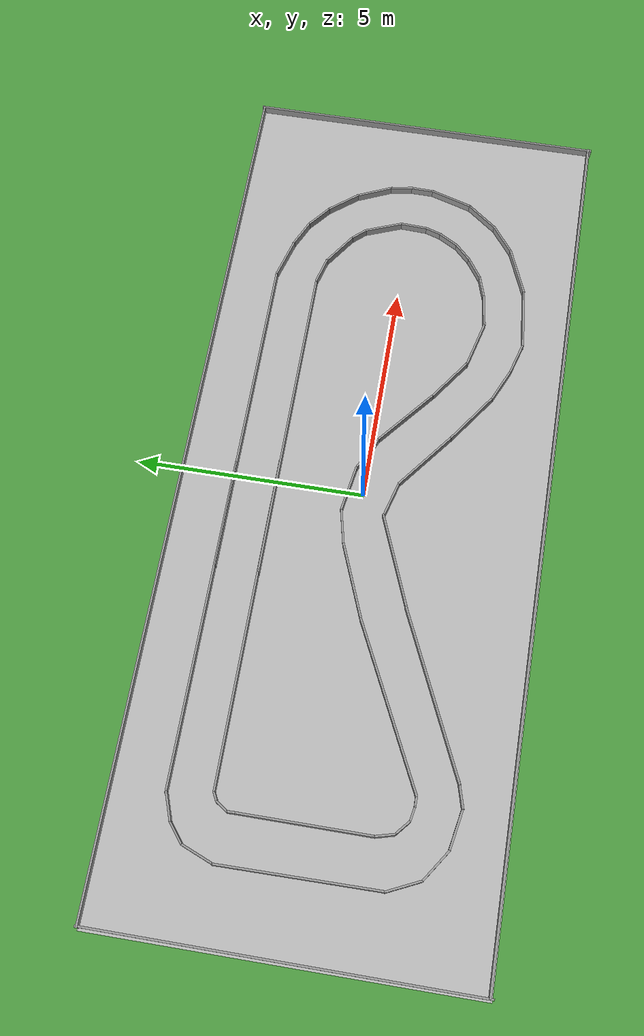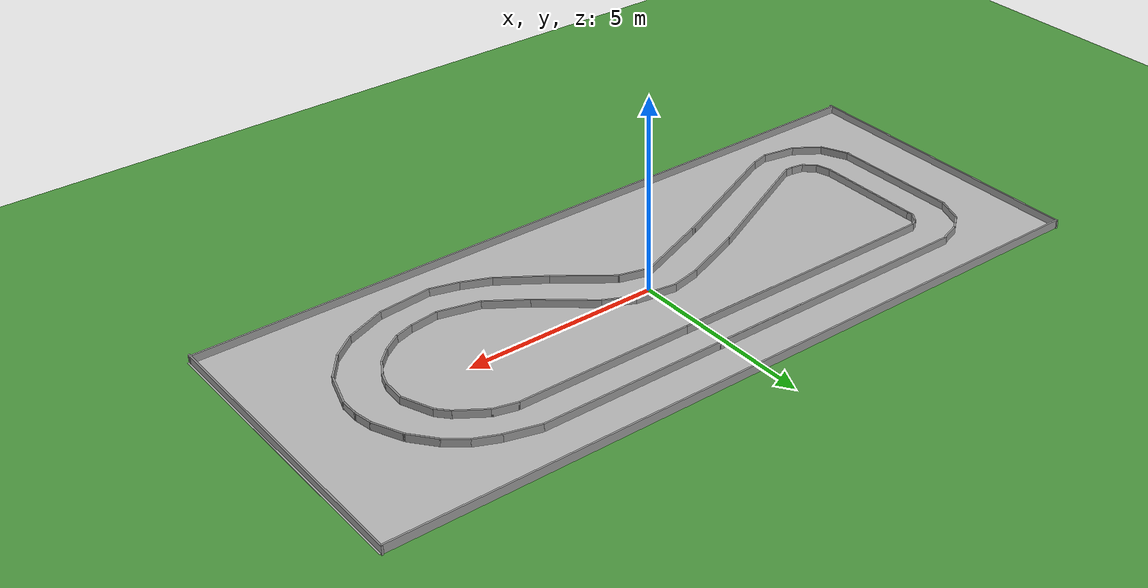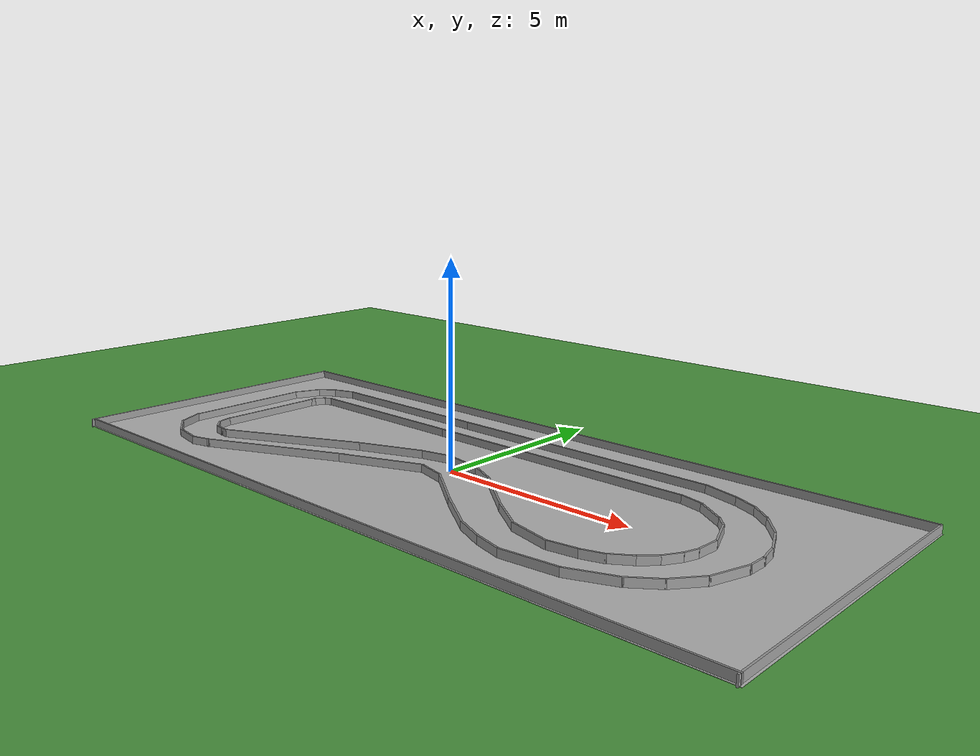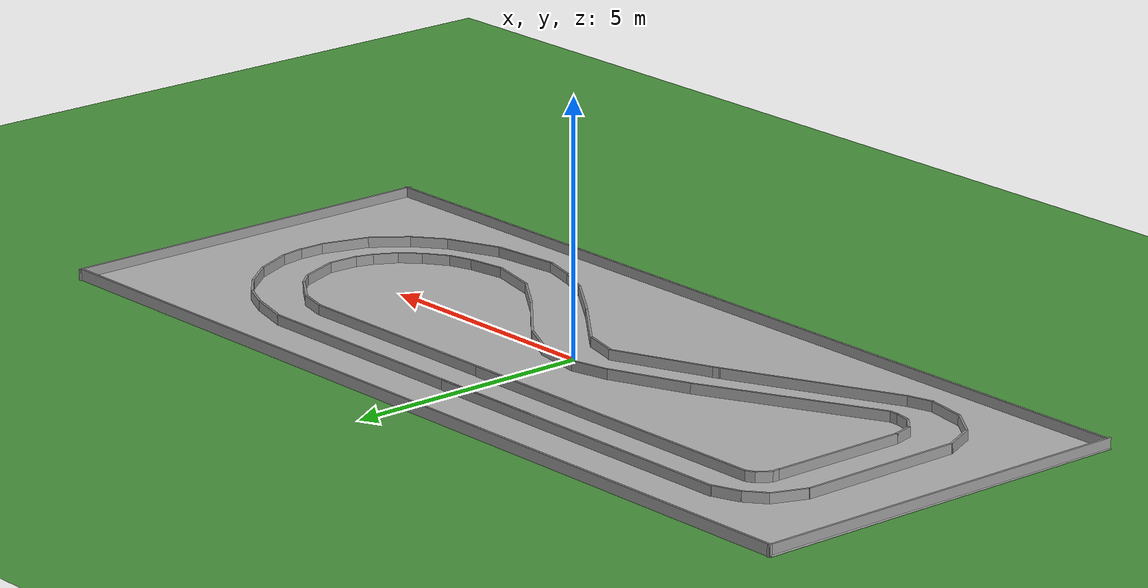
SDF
<sdf version="1.5">
 <world name="default">
  <light name="sun" type="directional">
   <cast_shadows>0</cast_shadows>
   <pose>0 0 10 0 -0 0</pose>
   <diffuse>0.8 0.8 0.8 1</diffuse>
   <specular>0.2 0.2 0.2 1</specular>
   <attenuation>
    <range>1000</range>
    <constant>0.9</constant>
    <linear>0.01</linear>
    <quadratic>0.001</quadratic>
   </attenuation>
   <direction>-0.5 0.1 -0.9</direction>
  </light>
  <scene>
   <sky><clouds><speed>1</speed></clouds></sky>
   <ambient>0.4 0.4 0.4 1</ambient>
   <background>0.7 0.7 0.7 1</background>
   <shadows>1</shadows>
  </scene>
  <physics name="default_physics" default="0" type="ode">
   <real_time_update_rate>1000</real_time_update_rate>
   <ode>
    <solver>
     <type>quick</type>
     <iters>70</iters>
     <sor>1.3</sor>
     <use_dynamic_moi_rescaling>0</use_dynamic_moi_rescaling>
    </solver>
    <constraints>
     <cfm>0</cfm>
     <erp>0.2</erp>
     <contact_max_correcting_vel>100</contact_max_correcting_vel>
     <contact_surface_layer>0.001</contact_surface_layer>
    </constraints>
   </ode>
   <max_step_size>0.001</max_step_size>
   <real_time_factor>1</real_time_factor>
  </physics>
  <scene><ambient>0.4 0.4 0.4 1</ambient><background>0.7 0.7 0.7 1</background><shadows>1</shadows></scene>
  <spherical_coordinates>
   <surface_model>EARTH_WGS84</surface_model>
   <latitude_deg>0</latitude_deg>
   <longitude_deg>0</longitude_deg>
   <elevation>0</elevation>
   <heading_deg>0</heading_deg>
  </spherical_coordinates>
  <model name="ground_grass">
   <static>1</static>
   <link name="ground_grass">
    <collision name="collision">
     <geometry><plane><normal>0 0 1</normal><size>50 50</size></plane></geometry>
     <surface><friction><ode><mu>100</mu><mu2>50</mu2></ode></friction></surface>
    </collision>
    <visual name="visual_ground">
     <cast_shadows>0</cast_shadows>
     <pose>0 0 0.005 0 -0 0</pose>
     <geometry><plane><normal>0 0 1</normal><size>50 50</size></plane></geometry>
     <material>
      <script>
       <uri>model://ground_grass/materials/scripts</uri>
       <uri>model://ground_grass/materials/textures</uri>
       <name>Floor/Grass</name>
      </script>
     </material>
    </visual>
    <velocity_decay><linear>0</linear><angular>0</angular></velocity_decay>
   </link>
  </model>
  <model name="ucsd_track_v1">
   <static>1</static>
   <link name="link_track">
    <collision name="collision">
     <geometry><plane><normal>0 0 1</normal><size>19.431 8.0264</size></plane></geometry>
     <surface><friction><ode><mu>100</mu><mu2>50</mu2></ode></friction></surface>
    </collision>
    <visual name="visual_ground">
     <cast_shadows>0</cast_shadows>
     <pose>0 0 0.005 0 -0 0</pose>
     <geometry><plane><normal>0 0 1</normal><size>19.431 8.0264</size></plane></geometry>
     <material>
      <script>
       <uri>model://ucsd_track_v1/materials/scripts</uri>
       <uri>model://ucsd_track_v1/materials/textures</uri>
       <name>Floor/Image</name>
      </script>
     </material>
    </visual>
    <velocity_decay><linear>0</linear><angular>0</angular></velocity_decay>
   </link>
   <pose>0 0 0.001 0 -0 0</pose>
  </model>
  <gravity>0 0 -9.8</gravity>
  <magnetic_field>6e-06 2.3e-05 -4.2e-05</magnetic_field>
  <atmosphere type="adiabatic"/>
  <model name="grey_wall_1">
   <link name="link">
    <pose>0 0 1.4 0 0 -0.660395</pose>
    <inertial>
     <inertia><ixx>nan</ixx><ixy>0</ixy><ixz>0</ixz><iyy>nan</iyy><iyz>0</iyz><izz>nan</izz></inertia>
     <mass>0</mass>
    </inertial>
    <visual name="visual">
     <cast_shadows>0</cast_shadows>
     <geometry><box><size>1.62445 0.043266 0.226147</size></box></geometry>
     <material>
      <script>
       <uri>model://grey_wall/materials/scripts</uri>
       <uri>model://grey_wall/materials/textures</uri>
       <name>vrc/grey_wall</name>
      </script>
      <ambient>1 1 1 1</ambient>
      <diffuse>1 1 1 1</diffuse>
      <specular>0 0 0 1</specular>
      <emissive>0 0 0 1</emissive>
     </material>
    </visual>
    <collision name="collision">
     <geometry><box><size>1.62445 0.043266 0.226147</size></box></geometry>
     <surface>
      <friction>
       <ode><mu>1</mu><mu2>1</mu2><fdir1>0 0 0</fdir1><slip1>0</slip1><slip2>0</slip2></ode>
       <torsional>
        <coefficient>1</coefficient>
        <patch_radius>0</patch_radius>
        <surface_radius>0</surface_radius>
        <use_patch_radius>1</use_patch_radius>
        <ode><slip>0</slip></ode>
       </torsional>
      </friction>
      <bounce><restitution_coefficient>0</restitution_coefficient><threshold>1e+06</threshold></bounce>
      <contact>
       <collide_without_contact>0</collide_without_contact>
       <collide_without_contact_bitmask>1</collide_without_contact_bitmask>
       <collide_bitmask>1</collide_bitmask>
       <ode>
        <soft_cfm>0</soft_cfm>
        <soft_erp>0.2</soft_erp>
        <kp>1e+13</kp>
        <kd>1</kd>
        <max_vel>0.01</max_vel>
        <min_depth>0</min_depth>
       </ode>
       <bullet>
        <split_impulse>1</split_impulse>
        <split_impulse_penetration_threshold>-0.01</split_impulse_penetration_threshold>
        <soft_cfm>0</soft_cfm>
        <soft_erp>0.2</soft_erp>
        <kp>1e+13</kp>
        <kd>1</kd>
       </bullet>
      </contact>
     </surface>
    </collision>
   </link>
   <static>1</static>
   <pose>0.973487 -1.21034 -1.30469 0 -0 0</pose>
  </model>
  <model name="grey_wall_2">
   <link name="link">
    <pose>0 0 1.4 0 -0 0</pose>
    <inertial>
     <inertia><ixx>nan</ixx><ixy>0</ixy><ixz>0</ixz><iyy>nan</iyy><iyz>0</iyz><izz>nan</izz></inertia>
     <mass>0</mass>
    </inertial>
    <visual name="visual">
     <cast_shadows>0</cast_shadows>
     <geometry><box><size>7.20978 0.043266 0.226147</size></box></geometry>
     <material>
      <script>
       <uri>model://grey_wall/materials/scripts</uri>
       <uri>model://grey_wall/materials/textures</uri>
       <name>vrc/grey_wall</name>
      </script>
      <ambient>1 1 1 1</ambient>
      <diffuse>1 1 1 1</diffuse>
      <specular>0 0 0 1</specular>
      <emissive>0 0 0 1</emissive>
     </material>
    </visual>
    <collision name="collision">
     <geometry><box><size>7.20978 0.043266 0.226147</size></box></geometry>
     <surface>
      <friction>
       <ode><mu>1</mu><mu2>1</mu2><fdir1>0 0 0</fdir1><slip1>0</slip1><slip2>0</slip2></ode>
       <torsional>
        <coefficient>1</coefficient>
        <patch_radius>0</patch_radius>
        <surface_radius>0</surface_radius>
        <use_patch_radius>1</use_patch_radius>
        <ode><slip>0</slip></ode>
       </torsional>
      </friction>
      <bounce><restitution_coefficient>0</restitution_coefficient><threshold>1e+06</threshold></bounce>
      <contact>
       <collide_without_contact>0</collide_without_contact>
       <collide_without_contact_bitmask>1</collide_without_contact_bitmask>
       <collide_bitmask>1</collide_bitmask>
       <ode>
        <soft_cfm>0</soft_cfm>
        <soft_erp>0.2</soft_erp>
        <kp>1e+13</kp>
        <kd>1</kd>
        <max_vel>0.01</max_vel>
        <min_depth>0</min_depth>
       </ode>
       <bullet>
        <split_impulse>1</split_impulse>
        <split_impulse_penetration_threshold>-0.01</split_impulse_penetration_threshold>
        <soft_cfm>0</soft_cfm>
        <soft_erp>0.2</soft_erp>
        <kp>1e+13</kp>
        <kd>1</kd>
       </bullet>
      </contact>
     </surface>
    </collision>
   </link>
   <static>1</static>
   <pose>-3.31818 2.85803 -1.30759 0 -0 0</pose>
  </model>
  <model name="grey_wall_3">
   <link name="link">
    <pose>0.713484 -0.011654 1.4 0 -0 0</pose>
    <inertial>
     <inertia><ixx>nan</ixx><ixy>0</ixy><ixz>0</ixz><iyy>nan</iyy><iyz>0</iyz><izz>nan</izz></inertia>
     <mass>0</mass>
    </inertial>
    <visual name="visual">
     <cast_shadows>0</cast_shadows>
     <geometry><box><size>19.3332 0.043266 0.226147</size></box></geometry>
     <material>
      <script>
       <uri>model://grey_wall/materials/scripts</uri>
       <uri>model://grey_wall/materials/textures</uri>
       <name>vrc/grey_wall</name>
      </script>
      <ambient>1 1 1 1</ambient>
      <diffuse>1 1 1 1</diffuse>
      <specular>0 0 0 1</specular>
      <emissive>0 0 0 1</emissive>
     </material>
    </visual>
    <collision name="collision">
     <geometry><box><size>19.3332 0.043266 0.226147</size></box></geometry>
     <surface>
      <friction>
       <ode><mu>1</mu><mu2>1</mu2><fdir1>0 0 0</fdir1><slip1>0</slip1><slip2>0</slip2></ode>
       <torsional>
        <coefficient>1</coefficient>
        <patch_radius>0</patch_radius>
        <surface_radius>0</surface_radius>
        <use_patch_radius>1</use_patch_radius>
        <ode><slip>0</slip></ode>
       </torsional>
      </friction>
      <bounce><restitution_coefficient>0</restitution_coefficient><threshold>1e+06</threshold></bounce>
      <contact>
       <collide_without_contact>0</collide_without_contact>
       <collide_without_contact_bitmask>1</collide_without_contact_bitmask>
       <collide_bitmask>1</collide_bitmask>
       <ode>
        <soft_cfm>0</soft_cfm>
        <soft_erp>0.2</soft_erp>
        <kp>1e+13</kp>
        <kd>1</kd>
        <max_vel>0.01</max_vel>
        <min_depth>0</min_depth>
       </ode>
       <bullet>
        <split_impulse>1</split_impulse>
        <split_impulse_penetration_threshold>-0.01</split_impulse_penetration_threshold>
        <soft_cfm>0</soft_cfm>
        <soft_erp>0.2</soft_erp>
        <kp>1e+13</kp>
        <kd>1</kd>
       </bullet>
      </contact>
     </surface>
    </collision>
   </link>
   <static>1</static>
   <pose>-0.716038 4.0109 -1.30508 0 -0 0</pose>
  </model>
  <model name="grey_wall_4">
   <link name="link">
    <pose>0.713484 -0.011654 1.4 0 -0 0</pose>
    <inertial>
     <inertia><ixx>nan</ixx><ixy>0</ixy><ixz>0</ixz><iyy>nan</iyy><iyz>0</iyz><izz>nan</izz></inertia>
     <mass>0</mass>
    </inertial>
    <visual name="visual">
     <cast_shadows>0</cast_shadows>
     <geometry><box><size>19.3332 0.043266 0.226147</size></box></geometry>
     <material>
      <script>
       <uri>model://grey_wall/materials/scripts</uri>
       <uri>model://grey_wall/materials/textures</uri>
       <name>vrc/grey_wall</name>
      </script>
      <ambient>1 1 1 1</ambient>
      <diffuse>1 1 1 1</diffuse>
      <specular>0 0 0 1</specular>
      <emissive>0 0 0 1</emissive>
     </material>
    </visual>
    <collision name="collision">
     <geometry><box><size>19.3332 0.043266 0.226147</size></box></geometry>
     <surface>
      <friction>
       <ode><mu>1</mu><mu2>1</mu2><fdir1>0 0 0</fdir1><slip1>0</slip1><slip2>0</slip2></ode>
       <torsional>
        <coefficient>1</coefficient>
        <patch_radius>0</patch_radius>
        <surface_radius>0</surface_radius>
        <use_patch_radius>1</use_patch_radius>
        <ode><slip>0</slip></ode>
       </torsional>
      </friction>
      <bounce><restitution_coefficient>0</restitution_coefficient><threshold>1e+06</threshold></bounce>
      <contact>
       <collide_without_contact>0</collide_without_contact>
       <collide_without_contact_bitmask>1</collide_without_contact_bitmask>
       <collide_bitmask>1</collide_bitmask>
       <ode>
        <soft_cfm>0</soft_cfm>
        <soft_erp>0.2</soft_erp>
        <kp>1e+13</kp>
        <kd>1</kd>
        <max_vel>0.01</max_vel>
        <min_depth>0</min_depth>
       </ode>
       <bullet>
        <split_impulse>1</split_impulse>
        <split_impulse_penetration_threshold>-0.01</split_impulse_penetration_threshold>
        <soft_cfm>0</soft_cfm>
        <soft_erp>0.2</soft_erp>
        <kp>1e+13</kp>
        <kd>1</kd>
       </bullet>
      </contact>
     </surface>
    </collision>
   </link>
   <static>1</static>
   <pose>-0.701966 -3.93959 -1.30508 0 -0 0</pose>
  </model>
  <model name="grey_wall_5">
   <link name="link">
    <pose>-0.467859 -0.097477 1.4 0 -0 0.009516</pose>
    <inertial>
     <inertia><ixx>nan</ixx><ixy>0</ixy><ixz>0</ixz><iyy>nan</iyy><iyz>0</iyz><izz>nan</izz></inertia>
     <mass>0</mass>
    </inertial>
    <visual name="visual">
     <cast_shadows>0</cast_shadows>
     <geometry><box><size>8.07319 0.043266 0.226147</size></box></geometry>
     <material>
      <script>
       <uri>model://grey_wall/materials/scripts</uri>
       <uri>model://grey_wall/materials/textures</uri>
       <name>vrc/grey_wall</name>
      </script>
      <ambient>1 1 1 1</ambient>
      <diffuse>1 1 1 1</diffuse>
      <specular>0 0 0 1</specular>
      <emissive>0 0 0 1</emissive>
     </material>
    </visual>
    <collision name="collision">
     <geometry><box><size>8.07319 0.043266 0.226147</size></box></geometry>
     <surface>
      <friction>
       <ode><mu>1</mu><mu2>1</mu2><fdir1>0 0 0</fdir1><slip1>0</slip1><slip2>0</slip2></ode>
       <torsional>
        <coefficient>1</coefficient>
        <patch_radius>0</patch_radius>
        <surface_radius>0</surface_radius>
        <use_patch_radius>1</use_patch_radius>
        <ode><slip>0</slip></ode>
       </torsional>
      </friction>
      <bounce><restitution_coefficient>0</restitution_coefficient><threshold>1e+06</threshold></bounce>
      <contact>
       <collide_without_contact>0</collide_without_contact>
       <collide_without_contact_bitmask>1</collide_without_contact_bitmask>
       <collide_bitmask>1</collide_bitmask>
       <ode>
        <soft_cfm>0</soft_cfm>
        <soft_erp>0.2</soft_erp>
        <kp>1e+13</kp>
        <kd>1</kd>
        <max_vel>0.01</max_vel>
        <min_depth>0</min_depth>
       </ode>
       <bullet>
        <split_impulse>1</split_impulse>
        <split_impulse_penetration_threshold>-0.01</split_impulse_penetration_threshold>
        <soft_cfm>0</soft_cfm>
        <soft_erp>0.2</soft_erp>
        <kp>1e+13</kp>
        <kd>1</kd>
       </bullet>
      </contact>
     </surface>
    </collision>
   </link>
   <static>1</static>
   <pose>-9.73387 0.474906 -1.30963 0 -0 1.55954</pose>
  </model>
  <model name="grey_wall_6">
   <link name="link">
    <pose>-0.467859 -0.097477 1.4 0 -0 0.009516</pose>
    <inertial>
     <inertia><ixx>nan</ixx><ixy>0</ixy><ixz>0</ixz><iyy>nan</iyy><iyz>0</iyz><izz>nan</izz></inertia>
     <mass>0</mass>
    </inertial>
    <visual name="visual">
     <cast_shadows>0</cast_shadows>
     <geometry><box><size>8.07319 0.043266 0.226147</size></box></geometry>
     <material>
      <script>
       <uri>model://grey_wall/materials/scripts</uri>
       <uri>model://grey_wall/materials/textures</uri>
       <name>vrc/grey_wall</name>
      </script>
      <ambient>1 1 1 1</ambient>
      <diffuse>1 1 1 1</diffuse>
      <specular>0 0 0 1</specular>
      <emissive>0 0 0 1</emissive>
     </material>
    </visual>
    <collision name="collision">
     <geometry><box><size>8.07319 0.043266 0.226147</size></box></geometry>
     <surface>
      <friction>
       <ode><mu>1</mu><mu2>1</mu2><fdir1>0 0 0</fdir1><slip1>0</slip1><slip2>0</slip2></ode>
       <torsional>
        <coefficient>1</coefficient>
        <patch_radius>0</patch_radius>
        <surface_radius>0</surface_radius>
        <use_patch_radius>1</use_patch_radius>
        <ode><slip>0</slip></ode>
       </torsional>
      </friction>
      <bounce><restitution_coefficient>0</restitution_coefficient><threshold>1e+06</threshold></bounce>
      <contact>
       <collide_without_contact>0</collide_without_contact>
       <collide_without_contact_bitmask>1</collide_without_contact_bitmask>
       <collide_bitmask>1</collide_bitmask>
       <ode>
        <soft_cfm>0</soft_cfm>
        <soft_erp>0.2</soft_erp>
        <kp>1e+13</kp>
        <kd>1</kd>
        <max_vel>0.01</max_vel>
        <min_depth>0</min_depth>
       </ode>
       <bullet>
        <split_impulse>1</split_impulse>
        <split_impulse_penetration_threshold>-0.01</split_impulse_penetration_threshold>
        <soft_cfm>0</soft_cfm>
        <soft_erp>0.2</soft_erp>
        <kp>1e+13</kp>
        <kd>1</kd>
       </bullet>
      </contact>
     </surface>
    </collision>
   </link>
   <static>1</static>
   <pose>9.55959 0.474995 -1.30963 0 -0 1.55954</pose>
  </model>
  <model name="grey_wall_7">
   <link name="link">
    <pose>-0.064175 -0.02969 1.4 0 -0 0.020488</pose>
    <inertial>
     <inertia><ixx>nan</ixx><ixy>0</ixy><ixz>0</ixz><iyy>nan</iyy><iyz>0</iyz><izz>nan</izz></inertia>
     <mass>0</mass>
    </inertial>
    <visual name="visual">
     <cast_shadows>0</cast_shadows>
     <geometry><box><size>3.42398 0.043266 0.226147</size></box></geometry>
     <material>
      <script>
       <uri>model://grey_wall/materials/scripts</uri>
       <uri>model://grey_wall/materials/textures</uri>
       <name>vrc/grey_wall</name>
      </script>
      <ambient>1 1 1 1</ambient>
      <diffuse>1 1 1 1</diffuse>
      <specular>0 0 0 1</specular>
      <emissive>0 0 0 1</emissive>
     </material>
    </visual>
    <collision name="collision">
     <geometry><box><size>3.42398 0.043266 0.226147</size></box></geometry>
     <surface>
      <friction>
       <ode><mu>1</mu><mu2>1</mu2><fdir1>0 0 0</fdir1><slip1>0</slip1><slip2>0</slip2></ode>
       <torsional>
        <coefficient>1</coefficient>
        <patch_radius>0</patch_radius>
        <surface_radius>0</surface_radius>
        <use_patch_radius>1</use_patch_radius>
        <ode><slip>0</slip></ode>
       </torsional>
      </friction>
      <bounce><restitution_coefficient>0</restitution_coefficient><threshold>1e+06</threshold></bounce>
      <contact>
       <collide_without_contact>0</collide_without_contact>
       <collide_without_contact_bitmask>1</collide_without_contact_bitmask>
       <collide_bitmask>1</collide_bitmask>
       <ode>
        <soft_cfm>0</soft_cfm>
        <soft_erp>0.2</soft_erp>
        <kp>1e+13</kp>
        <kd>1</kd>
        <max_vel>0.01</max_vel>
        <min_depth>0</min_depth>
       </ode>
       <bullet>
        <split_impulse>1</split_impulse>
        <split_impulse_penetration_threshold>-0.01</split_impulse_penetration_threshold>
        <soft_cfm>0</soft_cfm>
        <soft_erp>0.2</soft_erp>
        <kp>1e+13</kp>
        <kd>1</kd>
       </bullet>
      </contact>
     </surface>
    </collision>
   </link>
   <static>1</static>
   <pose>-8.11068 0.042246 -1.30963 0 -0 1.55954</pose>
  </model>
  <model name="grey_wall_8">
   <link name="link">
    <pose>0.112948 -0.0488 1.4 0 0 -0.362822</pose>
    <inertial>
     <inertia><ixx>nan</ixx><ixy>0</ixy><ixz>0</ixz><iyy>nan</iyy><iyz>0</iyz><izz>nan</izz></inertia>
     <mass>0</mass>
    </inertial>
    <visual name="visual">
     <cast_shadows>0</cast_shadows>
     <geometry><box><size>0.753854 0.043266 0.226147</size></box></geometry>
     <material>
      <script>
       <uri>model://grey_wall/materials/scripts</uri>
       <uri>model://grey_wall/materials/textures</uri>
       <name>vrc/grey_wall</name>
      </script>
      <ambient>1 1 1 1</ambient>
      <diffuse>1 1 1 1</diffuse>
      <specular>0 0 0 1</specular>
      <emissive>0 0 0 1</emissive>
     </material>
    </visual>
    <collision name="collision">
     <geometry><box><size>0.753854 0.043266 0.226147</size></box></geometry>
     <surface>
      <friction>
       <ode><mu>1</mu><mu2>1</mu2><fdir1>0 0 0</fdir1><slip1>0</slip1><slip2>0</slip2></ode>
       <torsional>
        <coefficient>1</coefficient>
        <patch_radius>0</patch_radius>
        <surface_radius>0</surface_radius>
        <use_patch_radius>1</use_patch_radius>
        <ode><slip>0</slip></ode>
       </torsional>
      </friction>
      <bounce><restitution_coefficient>0</restitution_coefficient><threshold>1e+06</threshold></bounce>
      <contact>
       <collide_without_contact>0</collide_without_contact>
       <collide_without_contact_bitmask>1</collide_without_contact_bitmask>
       <collide_bitmask>1</collide_bitmask>
       <ode>
        <soft_cfm>0</soft_cfm>
        <soft_erp>0.2</soft_erp>
        <kp>1e+13</kp>
        <kd>1</kd>
        <max_vel>0.01</max_vel>
        <min_depth>0</min_depth>
       </ode>
       <bullet>
        <split_impulse>1</split_impulse>
        <split_impulse_penetration_threshold>-0.01</split_impulse_penetration_threshold>
        <soft_cfm>0</soft_cfm>
        <soft_erp>0.2</soft_erp>
        <kp>1e+13</kp>
        <kd>1</kd>
       </bullet>
      </contact>
     </surface>
    </collision>
   </link>
   <static>1</static>
   <pose>-8.0118 1.89691 -1.30963 0 -0 1.55954</pose>
  </model>
  <model name="grey_wall_9">
   <link name="link">
    <pose>-0.058506 -0.047315 1.4 0 -0 0.675401</pose>
    <inertial>
     <inertia><ixx>nan</ixx><ixy>0</ixy><ixz>0</ixz><iyy>nan</iyy><iyz>0</iyz><izz>nan</izz></inertia>
     <mass>0</mass>
    </inertial>
    <visual name="visual">
     <cast_shadows>0</cast_shadows>
     <geometry><box><size>0.500666 0.043266 0.226147</size></box></geometry>
     <material>
      <script>
       <uri>model://grey_wall/materials/scripts</uri>
       <uri>model://grey_wall/materials/textures</uri>
       <name>vrc/grey_wall</name>
      </script>
      <ambient>1 1 1 1</ambient>
      <diffuse>1 1 1 1</diffuse>
      <specular>0 0 0 1</specular>
      <emissive>0 0 0 1</emissive>
     </material>
    </visual>
    <collision name="collision">
     <geometry><box><size>0.500666 0.043266 0.226147</size></box></geometry>
     <surface>
      <friction>
       <ode><mu>1</mu><mu2>1</mu2><fdir1>0 0 0</fdir1><slip1>0</slip1><slip2>0</slip2></ode>
       <torsional>
        <coefficient>1</coefficient>
        <patch_radius>0</patch_radius>
        <surface_radius>0</surface_radius>
        <use_patch_radius>1</use_patch_radius>
        <ode><slip>0</slip></ode>
       </torsional>
      </friction>
      <bounce><restitution_coefficient>0</restitution_coefficient><threshold>1e+06</threshold></bounce>
      <contact>
       <collide_without_contact>0</collide_without_contact>
       <collide_without_contact_bitmask>1</collide_without_contact_bitmask>
       <collide_bitmask>1</collide_bitmask>
       <ode>
        <soft_cfm>0</soft_cfm>
        <soft_erp>0.2</soft_erp>
        <kp>1e+13</kp>
        <kd>1</kd>
        <max_vel>0.01</max_vel>
        <min_depth>0</min_depth>
       </ode>
       <bullet>
        <split_impulse>1</split_impulse>
        <split_impulse_penetration_threshold>-0.01</split_impulse_penetration_threshold>
        <soft_cfm>0</soft_cfm>
        <soft_erp>0.2</soft_erp>
        <kp>1e+13</kp>
        <kd>1</kd>
       </bullet>
      </contact>
     </surface>
    </collision>
   </link>
   <static>1</static>
   <pose>-7.5792 2.5463 -1.30539 0 -0 0</pose>
  </model>
  <model name="grey_wall_10">
   <link name="link">
    <pose>-0.124295 -0.038559 1.4 0 -0 0.344466</pose>
    <inertial>
     <inertia><ixx>nan</ixx><ixy>0</ixy><ixz>0</ixz><iyy>nan</iyy><iyz>0</iyz><izz>nan</izz></inertia>
     <mass>0</mass>
    </inertial>
    <visual name="visual">
     <cast_shadows>0</cast_shadows>
     <geometry><box><size>0.619827 0.043266 0.226147</size></box></geometry>
     <material>
      <script>
       <uri>model://grey_wall/materials/scripts</uri>
       <uri>model://grey_wall/materials/textures</uri>
       <name>vrc/grey_wall</name>
      </script>
      <ambient>1 1 1 1</ambient>
      <diffuse>1 1 1 1</diffuse>
      <specular>0 0 0 1</specular>
      <emissive>0 0 0 1</emissive>
     </material>
    </visual>
    <collision name="collision">
     <geometry><box><size>0.619827 0.043266 0.226147</size></box></geometry>
     <surface>
      <friction>
       <ode><mu>1</mu><mu2>1</mu2><fdir1>0 0 0</fdir1><slip1>0</slip1><slip2>0</slip2></ode>
       <torsional>
        <coefficient>1</coefficient>
        <patch_radius>0</patch_radius>
        <surface_radius>0</surface_radius>
        <use_patch_radius>1</use_patch_radius>
        <ode><slip>0</slip></ode>
       </torsional>
      </friction>
      <bounce><restitution_coefficient>0</restitution_coefficient><threshold>1e+06</threshold></bounce>
      <contact>
       <collide_without_contact>0</collide_without_contact>
       <collide_without_contact_bitmask>1</collide_without_contact_bitmask>
       <collide_bitmask>1</collide_bitmask>
       <ode>
        <soft_cfm>0</soft_cfm>
        <soft_erp>0.2</soft_erp>
        <kp>1e+13</kp>
        <kd>1</kd>
        <max_vel>0.01</max_vel>
        <min_depth>0</min_depth>
       </ode>
       <bullet>
        <split_impulse>1</split_impulse>
        <split_impulse_penetration_threshold>-0.01</split_impulse_penetration_threshold>
        <soft_cfm>0</soft_cfm>
        <soft_erp>0.2</soft_erp>
        <kp>1e+13</kp>
        <kd>1</kd>
       </bullet>
      </contact>
     </surface>
    </collision>
   </link>
   <static>1</static>
   <pose>-7.0396 2.79261 -1.30539 0 -0 0</pose>
  </model>
  <model name="grey_wall_11">
   <link name="link">
    <pose>-0.026662 0.026915 1.4 0 -0 0.431274</pose>
    <inertial>
     <inertia><ixx>nan</ixx><ixy>0</ixy><ixz>0</ixz><iyy>nan</iyy><iyz>0</iyz><izz>nan</izz></inertia>
     <mass>0</mass>
    </inertial>
    <visual name="visual">
     <cast_shadows>0</cast_shadows>
     <geometry><box><size>3.81606 0.043266 0.226147</size></box></geometry>
     <material>
      <script>
       <uri>model://grey_wall/materials/scripts</uri>
       <uri>model://grey_wall/materials/textures</uri>
       <name>vrc/grey_wall</name>
      </script>
      <ambient>1 1 1 1</ambient>
      <diffuse>1 1 1 1</diffuse>
      <specular>0 0 0 1</specular>
      <emissive>0 0 0 1</emissive>
     </material>
    </visual>
    <collision name="collision">
     <geometry><box><size>3.81606 0.043266 0.226147</size></box></geometry>
     <surface>
      <friction>
       <ode><mu>1</mu><mu2>1</mu2><fdir1>0 0 0</fdir1><slip1>0</slip1><slip2>0</slip2></ode>
       <torsional>
        <coefficient>1</coefficient>
        <patch_radius>0</patch_radius>
        <surface_radius>0</surface_radius>
        <use_patch_radius>1</use_patch_radius>
        <ode><slip>0</slip></ode>
       </torsional>
      </friction>
      <bounce><restitution_coefficient>0</restitution_coefficient><threshold>1e+06</threshold></bounce>
      <contact>
       <collide_without_contact>0</collide_without_contact>
       <collide_without_contact_bitmask>1</collide_without_contact_bitmask>
       <collide_bitmask>1</collide_bitmask>
       <ode>
        <soft_cfm>0</soft_cfm>
        <soft_erp>0.2</soft_erp>
        <kp>1e+13</kp>
        <kd>1</kd>
        <max_vel>0.01</max_vel>
        <min_depth>0</min_depth>
       </ode>
       <bullet>
        <split_impulse>1</split_impulse>
        <split_impulse_penetration_threshold>-0.01</split_impulse_penetration_threshold>
        <soft_cfm>0</soft_cfm>
        <soft_erp>0.2</soft_erp>
        <kp>1e+13</kp>
        <kd>1</kd>
       </bullet>
      </contact>
     </surface>
    </collision>
   </link>
   <static>1</static>
   <pose>-4.07016 -2.10175 -1.30331 0 -0 0</pose>
  </model>
  <model name="grey_wall_12">
   <link name="link">
    <pose>0 0 1.4 0 -0 0.382885</pose>
    <inertial>
     <inertia><ixx>nan</ixx><ixy>0</ixy><ixz>0</ixz><iyy>nan</iyy><iyz>0</iyz><izz>nan</izz></inertia>
     <mass>0</mass>
    </inertial>
    <visual name="visual">
     <cast_shadows>0</cast_shadows>
     <geometry><box><size>2.25374 0.043266 0.226147</size></box></geometry>
     <material>
      <script>
       <uri>model://grey_wall/materials/scripts</uri>
       <uri>model://grey_wall/materials/textures</uri>
       <name>vrc/grey_wall</name>
      </script>
      <ambient>1 1 1 1</ambient>
      <diffuse>1 1 1 1</diffuse>
      <specular>0 0 0 1</specular>
      <emissive>0 0 0 1</emissive>
     </material>
    </visual>
    <collision name="collision">
     <geometry><box><size>2.25374 0.043266 0.226147</size></box></geometry>
     <surface>
      <friction>
       <ode><mu>1</mu><mu2>1</mu2><fdir1>0 0 0</fdir1><slip1>0</slip1><slip2>0</slip2></ode>
       <torsional>
        <coefficient>1</coefficient>
        <patch_radius>0</patch_radius>
        <surface_radius>0</surface_radius>
        <use_patch_radius>1</use_patch_radius>
        <ode><slip>0</slip></ode>
       </torsional>
      </friction>
      <bounce><restitution_coefficient>0</restitution_coefficient><threshold>1e+06</threshold></bounce>
      <contact>
       <collide_without_contact>0</collide_without_contact>
       <collide_without_contact_bitmask>1</collide_without_contact_bitmask>
       <collide_bitmask>1</collide_bitmask>
       <ode>
        <soft_cfm>0</soft_cfm>
        <soft_erp>0.2</soft_erp>
        <kp>1e+13</kp>
        <kd>1</kd>
        <max_vel>0.01</max_vel>
        <min_depth>0</min_depth>
       </ode>
       <bullet>
        <split_impulse>1</split_impulse>
        <split_impulse_penetration_threshold>-0.01</split_impulse_penetration_threshold>
        <soft_cfm>0</soft_cfm>
        <soft_erp>0.2</soft_erp>
        <kp>1e+13</kp>
        <kd>1</kd>
       </bullet>
      </contact>
     </surface>
    </collision>
   </link>
   <static>1</static>
   <pose>-1.45423 -0.91787 -1.30539 0 -0 0</pose>
  </model>
  <model name="grey_wall_13">
   <link name="link">
    <pose>0 0 1.4 0 0 -0.265752</pose>
    <inertial>
     <inertia><ixx>nan</ixx><ixy>0</ixy><ixz>0</ixz><iyy>nan</iyy><iyz>0</iyz><izz>nan</izz></inertia>
     <mass>0</mass>
    </inertial>
    <visual name="visual">
     <cast_shadows>0</cast_shadows>
     <geometry><box><size>0.835499 0.043266 0.226147</size></box></geometry>
     <material>
      <script>
       <uri>model://grey_wall/materials/scripts</uri>
       <uri>model://grey_wall/materials/textures</uri>
       <name>vrc/grey_wall</name>
      </script>
      <ambient>1 1 1 1</ambient>
      <diffuse>1 1 1 1</diffuse>
      <specular>0 0 0 1</specular>
      <emissive>0 0 0 1</emissive>
     </material>
    </visual>
    <collision name="collision">
     <geometry><box><size>0.835499 0.043266 0.226147</size></box></geometry>
     <surface>
      <friction>
       <ode><mu>1</mu><mu2>1</mu2><fdir1>0 0 0</fdir1><slip1>0</slip1><slip2>0</slip2></ode>
       <torsional>
        <coefficient>1</coefficient>
        <patch_radius>0</patch_radius>
        <surface_radius>0</surface_radius>
        <use_patch_radius>1</use_patch_radius>
        <ode><slip>0</slip></ode>
       </torsional>
      </friction>
      <bounce><restitution_coefficient>0</restitution_coefficient><threshold>1e+06</threshold></bounce>
      <contact>
       <collide_without_contact>0</collide_without_contact>
       <collide_without_contact_bitmask>1</collide_without_contact_bitmask>
       <collide_bitmask>1</collide_bitmask>
       <ode>
        <soft_cfm>0</soft_cfm>
        <soft_erp>0.2</soft_erp>
        <kp>1e+13</kp>
        <kd>1</kd>
        <max_vel>0.01</max_vel>
        <min_depth>0</min_depth>
       </ode>
       <bullet>
        <split_impulse>1</split_impulse>
        <split_impulse_penetration_threshold>-0.01</split_impulse_penetration_threshold>
        <soft_cfm>0</soft_cfm>
        <soft_erp>0.2</soft_erp>
        <kp>1e+13</kp>
        <kd>1</kd>
       </bullet>
      </contact>
     </surface>
    </collision>
   </link>
   <static>1</static>
   <pose>-0.042418 -0.617739 -1.30539 0 -0 0</pose>
  </model>
  <model name="grey_wall_14">
   <link name="link">
    <pose>-0.07983 0.081676 1.4 0 0 -0.601795</pose>
    <inertial>
     <inertia><ixx>nan</ixx><ixy>0</ixy><ixz>0</ixz><iyy>nan</iyy><iyz>0</iyz><izz>nan</izz></inertia>
     <mass>0</mass>
    </inertial>
    <visual name="visual">
     <cast_shadows>0</cast_shadows>
     <geometry><box><size>0.789146 0.043266 0.226147</size></box></geometry>
     <material>
      <script>
       <uri>model://grey_wall/materials/scripts</uri>
       <uri>model://grey_wall/materials/textures</uri>
       <name>vrc/grey_wall</name>
      </script>
      <ambient>1 1 1 1</ambient>
      <diffuse>1 1 1 1</diffuse>
      <specular>0 0 0 1</specular>
      <emissive>0 0 0 1</emissive>
     </material>
    </visual>
    <collision name="collision">
     <geometry><box><size>0.789146 0.043266 0.226147</size></box></geometry>
     <surface>
      <friction>
       <ode><mu>1</mu><mu2>1</mu2><fdir1>0 0 0</fdir1><slip1>0</slip1><slip2>0</slip2></ode>
       <torsional>
        <coefficient>1</coefficient>
        <patch_radius>0</patch_radius>
        <surface_radius>0</surface_radius>
        <use_patch_radius>1</use_patch_radius>
        <ode><slip>0</slip></ode>
       </torsional>
      </friction>
      <bounce><restitution_coefficient>0</restitution_coefficient><threshold>1e+06</threshold></bounce>
      <contact>
       <collide_without_contact>0</collide_without_contact>
       <collide_without_contact_bitmask>1</collide_without_contact_bitmask>
       <collide_bitmask>1</collide_bitmask>
       <ode>
        <soft_cfm>0</soft_cfm>
        <soft_erp>0.2</soft_erp>
        <kp>1e+13</kp>
        <kd>1</kd>
        <max_vel>0.01</max_vel>
        <min_depth>0</min_depth>
       </ode>
       <bullet>
        <split_impulse>1</split_impulse>
        <split_impulse_penetration_threshold>-0.01</split_impulse_penetration_threshold>
        <soft_cfm>0</soft_cfm>
        <soft_erp>0.2</soft_erp>
        <kp>1e+13</kp>
        <kd>1</kd>
       </bullet>
      </contact>
     </surface>
    </collision>
   </link>
   <static>1</static>
   <pose>-7.35341 -2.70293 -1.30539 0 -0 0</pose>
  </model>
  <model name="grey_wall_15">
   <link name="link">
    <pose>0.107141 -0.075692 1.4 0 -0 2.00429</pose>
    <inertial>
     <inertia><ixx>nan</ixx><ixy>0</ixy><ixz>0</ixz><iyy>nan</iyy><iyz>0</iyz><izz>nan</izz></inertia>
     <mass>0</mass>
    </inertial>
    <visual name="visual">
     <cast_shadows>0</cast_shadows>
     <geometry><box><size>0.783473 0.043266 0.226147</size></box></geometry>
     <material>
      <script>
       <uri>model://grey_wall/materials/scripts</uri>
       <uri>model://grey_wall/materials/textures</uri>
       <name>vrc/grey_wall</name>
      </script>
      <ambient>1 1 1 1</ambient>
      <diffuse>1 1 1 1</diffuse>
      <specular>0 0 0 1</specular>
      <emissive>0 0 0 1</emissive>
     </material>
    </visual>
    <collision name="collision">
     <geometry><box><size>0.783473 0.043266 0.226147</size></box></geometry>
     <surface>
      <friction>
       <ode><mu>1</mu><mu2>1</mu2><fdir1>0 0 0</fdir1><slip1>0</slip1><slip2>0</slip2></ode>
       <torsional>
        <coefficient>1</coefficient>
        <patch_radius>0</patch_radius>
        <surface_radius>0</surface_radius>
        <use_patch_radius>1</use_patch_radius>
        <ode><slip>0</slip></ode>
       </torsional>
      </friction>
      <bounce><restitution_coefficient>0</restitution_coefficient><threshold>1e+06</threshold></bounce>
      <contact>
       <collide_without_contact>0</collide_without_contact>
       <collide_without_contact_bitmask>1</collide_without_contact_bitmask>
       <collide_bitmask>1</collide_bitmask>
       <ode>
        <soft_cfm>0</soft_cfm>
        <soft_erp>0.2</soft_erp>
        <kp>1e+13</kp>
        <kd>1</kd>
        <max_vel>0.01</max_vel>
        <min_depth>0</min_depth>
       </ode>
       <bullet>
        <split_impulse>1</split_impulse>
        <split_impulse_penetration_threshold>-0.01</split_impulse_penetration_threshold>
        <soft_cfm>0</soft_cfm>
        <soft_erp>0.2</soft_erp>
        <kp>1e+13</kp>
        <kd>1</kd>
       </bullet>
      </contact>
     </surface>
    </collision>
   </link>
   <static>1</static>
   <pose>-8.01965 -1.98265 -1.30539 0 -0 0</pose>
  </model>
  <model name="grey_wall_17">
   <link name="link">
    <pose>0 0 1.4 0 -0 0</pose>
    <inertial>
     <inertia><ixx>nan</ixx><ixy>0</ixy><ixz>0</ixz><iyy>nan</iyy><iyz>0</iyz><izz>nan</izz></inertia>
     <mass>0</mass>
    </inertial>
    <visual name="visual">
     <cast_shadows>0</cast_shadows>
     <geometry><box><size>7.20978 0.043266 0.226147</size></box></geometry>
     <material>
      <script>
       <uri>model://grey_wall/materials/scripts</uri>
       <uri>model://grey_wall/materials/textures</uri>
       <name>vrc/grey_wall</name>
      </script>
      <ambient>1 1 1 1</ambient>
      <diffuse>1 1 1 1</diffuse>
      <specular>0 0 0 1</specular>
      <emissive>0 0 0 1</emissive>
     </material>
    </visual>
    <collision name="collision">
     <geometry><box><size>7.20978 0.043266 0.226147</size></box></geometry>
     <surface>
      <friction>
       <ode><mu>1</mu><mu2>1</mu2><fdir1>0 0 0</fdir1><slip1>0</slip1><slip2>0</slip2></ode>
       <torsional>
        <coefficient>1</coefficient>
        <patch_radius>0</patch_radius>
        <surface_radius>0</surface_radius>
        <use_patch_radius>1</use_patch_radius>
        <ode><slip>0</slip></ode>
       </torsional>
      </friction>
      <bounce><restitution_coefficient>0</restitution_coefficient><threshold>1e+06</threshold></bounce>
      <contact>
       <collide_without_contact>0</collide_without_contact>
       <collide_without_contact_bitmask>1</collide_without_contact_bitmask>
       <collide_bitmask>1</collide_bitmask>
       <ode>
        <soft_cfm>0</soft_cfm>
        <soft_erp>0.2</soft_erp>
        <kp>1e+13</kp>
        <kd>1</kd>
        <max_vel>0.01</max_vel>
        <min_depth>0</min_depth>
       </ode>
       <bullet>
        <split_impulse>1</split_impulse>
        <split_impulse_penetration_threshold>-0.01</split_impulse_penetration_threshold>
        <soft_cfm>0</soft_cfm>
        <soft_erp>0.2</soft_erp>
        <kp>1e+13</kp>
        <kd>1</kd>
       </bullet>
      </contact>
     </surface>
    </collision>
   </link>
   <static>1</static>
   <pose>1.44796 1.9115 -1.30759 0 -0 0</pose>
  </model>
  <model name="grey_wall_18">
   <link name="link">
    <pose>0 0 1.4 0 -0 0</pose>
    <inertial>
     <inertia><ixx>nan</ixx><ixy>0</ixy><ixz>0</ixz><iyy>nan</iyy><iyz>0</iyz><izz>nan</izz></inertia>
     <mass>0</mass>
    </inertial>
    <visual name="visual">
     <cast_shadows>0</cast_shadows>
     <geometry><box><size>7.20978 0.043266 0.226147</size></box></geometry>
     <material>
      <script>
       <uri>model://grey_wall/materials/scripts</uri>
       <uri>model://grey_wall/materials/textures</uri>
       <name>vrc/grey_wall</name>
      </script>
      <ambient>1 1 1 1</ambient>
      <diffuse>1 1 1 1</diffuse>
      <specular>0 0 0 1</specular>
      <emissive>0 0 0 1</emissive>
     </material>
    </visual>
    <collision name="collision">
     <geometry><box><size>7.20978 0.043266 0.226147</size></box></geometry>
     <surface>
      <friction>
       <ode><mu>1</mu><mu2>1</mu2><fdir1>0 0 0</fdir1><slip1>0</slip1><slip2>0</slip2></ode>
       <torsional>
        <coefficient>1</coefficient>
        <patch_radius>0</patch_radius>
        <surface_radius>0</surface_radius>
        <use_patch_radius>1</use_patch_radius>
        <ode><slip>0</slip></ode>
       </torsional>
      </friction>
      <bounce><restitution_coefficient>0</restitution_coefficient><threshold>1e+06</threshold></bounce>
      <contact>
       <collide_without_contact>0</collide_without_contact>
       <collide_without_contact_bitmask>1</collide_without_contact_bitmask>
       <collide_bitmask>1</collide_bitmask>
       <ode>
        <soft_cfm>0</soft_cfm>
        <soft_erp>0.2</soft_erp>
        <kp>1e+13</kp>
        <kd>1</kd>
        <max_vel>0.01</max_vel>
        <min_depth>0</min_depth>
       </ode>
       <bullet>
        <split_impulse>1</split_impulse>
        <split_impulse_penetration_threshold>-0.01</split_impulse_penetration_threshold>
        <soft_cfm>0</soft_cfm>
        <soft_erp>0.2</soft_erp>
        <kp>1e+13</kp>
        <kd>1</kd>
       </bullet>
      </contact>
     </surface>
    </collision>
   </link>
   <static>1</static>
   <pose>1.47433 2.85123 -1.30759 0 -0 0</pose>
  </model>
  <model name="grey_wall_19">
   <link name="link">
    <pose>0.087469 0.011541 1.4 0 0 -0.183893</pose>
    <inertial>
     <inertia><ixx>nan</ixx><ixy>0</ixy><ixz>0</ixz><iyy>nan</iyy><iyz>0</iyz><izz>nan</izz></inertia>
     <mass>0</mass>
    </inertial>
    <visual name="visual">
     <cast_shadows>0</cast_shadows>
     <geometry><box><size>0.85162 0.043266 0.226147</size></box></geometry>
     <material>
      <script>
       <uri>model://grey_wall/materials/scripts</uri>
       <uri>model://grey_wall/materials/textures</uri>
       <name>vrc/grey_wall</name>
      </script>
      <ambient>1 1 1 1</ambient>
      <diffuse>1 1 1 1</diffuse>
      <specular>0 0 0 1</specular>
      <emissive>0 0 0 1</emissive>
     </material>
    </visual>
    <collision name="collision">
     <geometry><box><size>0.85162 0.043266 0.226147</size></box></geometry>
     <surface>
      <friction>
       <ode><mu>1</mu><mu2>1</mu2><fdir1>0 0 0</fdir1><slip1>0</slip1><slip2>0</slip2></ode>
       <torsional>
        <coefficient>1</coefficient>
        <patch_radius>0</patch_radius>
        <surface_radius>0</surface_radius>
        <use_patch_radius>1</use_patch_radius>
        <ode><slip>0</slip></ode>
       </torsional>
      </friction>
      <bounce><restitution_coefficient>0</restitution_coefficient><threshold>1e+06</threshold></bounce>
      <contact>
       <collide_without_contact>0</collide_without_contact>
       <collide_without_contact_bitmask>1</collide_without_contact_bitmask>
       <collide_bitmask>1</collide_bitmask>
       <ode>
        <soft_cfm>0</soft_cfm>
        <soft_erp>0.2</soft_erp>
        <kp>1e+13</kp>
        <kd>1</kd>
        <max_vel>0.01</max_vel>
        <min_depth>0</min_depth>
       </ode>
       <bullet>
        <split_impulse>1</split_impulse>
        <split_impulse_penetration_threshold>-0.01</split_impulse_penetration_threshold>
        <soft_cfm>0</soft_cfm>
        <soft_erp>0.2</soft_erp>
        <kp>1e+13</kp>
        <kd>1</kd>
       </bullet>
      </contact>
     </surface>
    </collision>
   </link>
   <static>1</static>
   <pose>-6.79091 -2.92555 -1.30539 0 -0 0</pose>
  </model>
  <model name="grey_wall_20">
   <link name="link">
    <pose>-0.003183 0.005606 1.4 0 -0 0.275384</pose>
    <inertial>
     <inertia><ixx>nan</ixx><ixy>0</ixy><ixz>0</ixz><iyy>nan</iyy><iyz>0</iyz><izz>nan</izz></inertia>
     <mass>0</mass>
    </inertial>
    <visual name="visual">
     <cast_shadows>0</cast_shadows>
     <geometry><box><size>0.558925 0.043266 0.226147</size></box></geometry>
     <material>
      <script>
       <uri>model://grey_wall/materials/scripts</uri>
       <uri>model://grey_wall/materials/textures</uri>
       <name>vrc/grey_wall</name>
      </script>
      <ambient>1 1 1 1</ambient>
      <diffuse>1 1 1 1</diffuse>
      <specular>0 0 0 1</specular>
      <emissive>0 0 0 1</emissive>
     </material>
    </visual>
    <collision name="collision">
     <geometry><box><size>0.558925 0.043266 0.226147</size></box></geometry>
     <surface>
      <friction>
       <ode><mu>1</mu><mu2>1</mu2><fdir1>0 0 0</fdir1><slip1>0</slip1><slip2>0</slip2></ode>
       <torsional>
        <coefficient>1</coefficient>
        <patch_radius>0</patch_radius>
        <surface_radius>0</surface_radius>
        <use_patch_radius>1</use_patch_radius>
        <ode><slip>0</slip></ode>
       </torsional>
      </friction>
      <bounce><restitution_coefficient>0</restitution_coefficient><threshold>1e+06</threshold></bounce>
      <contact>
       <collide_without_contact>0</collide_without_contact>
       <collide_without_contact_bitmask>1</collide_without_contact_bitmask>
       <collide_bitmask>1</collide_bitmask>
       <ode>
        <soft_cfm>0</soft_cfm>
        <soft_erp>0.2</soft_erp>
        <kp>1e+13</kp>
        <kd>1</kd>
        <max_vel>0.01</max_vel>
        <min_depth>0</min_depth>
       </ode>
       <bullet>
        <split_impulse>1</split_impulse>
        <split_impulse_penetration_threshold>-0.01</split_impulse_penetration_threshold>
        <soft_cfm>0</soft_cfm>
        <soft_erp>0.2</soft_erp>
        <kp>1e+13</kp>
        <kd>1</kd>
       </bullet>
      </contact>
     </surface>
    </collision>
   </link>
   <static>1</static>
   <pose>-6.02923 -2.92892 -1.30539 0 -0 0</pose>
  </model>
  <model name="grey_wall_21">
   <link name="link">
    <pose>0.035544 -0.032533 1.4 0 0 -0.276766</pose>
    <inertial>
     <inertia><ixx>nan</ixx><ixy>0</ixy><ixz>0</ixz><iyy>nan</iyy><iyz>0</iyz><izz>nan</izz></inertia>
     <mass>0</mass>
    </inertial>
    <visual name="visual">
     <cast_shadows>0</cast_shadows>
     <geometry><box><size>0.919493 0.043266 0.226147</size></box></geometry>
     <material>
      <script>
       <uri>model://grey_wall/materials/scripts</uri>
       <uri>model://grey_wall/materials/textures</uri>
       <name>vrc/grey_wall</name>
      </script>
      <ambient>1 1 1 1</ambient>
      <diffuse>1 1 1 1</diffuse>
      <specular>0 0 0 1</specular>
      <emissive>0 0 0 1</emissive>
     </material>
    </visual>
    <collision name="collision">
     <geometry><box><size>0.919493 0.043266 0.226147</size></box></geometry>
     <surface>
      <friction>
       <ode><mu>1</mu><mu2>1</mu2><fdir1>0 0 0</fdir1><slip1>0</slip1><slip2>0</slip2></ode>
       <torsional>
        <coefficient>1</coefficient>
        <patch_radius>0</patch_radius>
        <surface_radius>0</surface_radius>
        <use_patch_radius>1</use_patch_radius>
        <ode><slip>0</slip></ode>
       </torsional>
      </friction>
      <bounce><restitution_coefficient>0</restitution_coefficient><threshold>1e+06</threshold></bounce>
      <contact>
       <collide_without_contact>0</collide_without_contact>
       <collide_without_contact_bitmask>1</collide_without_contact_bitmask>
       <collide_bitmask>1</collide_bitmask>
       <ode>
        <soft_cfm>0</soft_cfm>
        <soft_erp>0.2</soft_erp>
        <kp>1e+13</kp>
        <kd>1</kd>
        <max_vel>0.01</max_vel>
        <min_depth>0</min_depth>
       </ode>
       <bullet>
        <split_impulse>1</split_impulse>
        <split_impulse_penetration_threshold>-0.01</split_impulse_penetration_threshold>
        <soft_cfm>0</soft_cfm>
        <soft_erp>0.2</soft_erp>
        <kp>1e+13</kp>
        <kd>1</kd>
       </bullet>
      </contact>
     </surface>
    </collision>
   </link>
   <static>1</static>
   <pose>5.47269 2.76103 -1.30469 0 -0 0</pose>
  </model>
  <model name="grey_wall_22">
   <link name="link">
    <pose>0.073037 -0.320766 1.4 0 -0 1.98383</pose>
    <inertial>
     <inertia><ixx>nan</ixx><ixy>0</ixy><ixz>0</ixz><iyy>nan</iyy><iyz>0</iyz><izz>nan</izz></inertia>
     <mass>0</mass>
    </inertial>
    <visual name="visual">
     <cast_shadows>0</cast_shadows>
     <geometry><box><size>0.873424 0.043266 0.226147</size></box></geometry>
     <material>
      <script>
       <uri>model://grey_wall/materials/scripts</uri>
       <uri>model://grey_wall/materials/textures</uri>
       <name>vrc/grey_wall</name>
      </script>
      <ambient>1 1 1 1</ambient>
      <diffuse>1 1 1 1</diffuse>
      <specular>0 0 0 1</specular>
      <emissive>0 0 0 1</emissive>
     </material>
    </visual>
    <collision name="collision">
     <geometry><box><size>0.873424 0.043266 0.226147</size></box></geometry>
     <surface>
      <friction>
       <ode><mu>1</mu><mu2>1</mu2><fdir1>0 0 0</fdir1><slip1>0</slip1><slip2>0</slip2></ode>
       <torsional>
        <coefficient>1</coefficient>
        <patch_radius>0</patch_radius>
        <surface_radius>0</surface_radius>
        <use_patch_radius>1</use_patch_radius>
        <ode><slip>0</slip></ode>
       </torsional>
      </friction>
      <bounce><restitution_coefficient>0</restitution_coefficient><threshold>1e+06</threshold></bounce>
      <contact>
       <collide_without_contact>0</collide_without_contact>
       <collide_without_contact_bitmask>1</collide_without_contact_bitmask>
       <collide_bitmask>1</collide_bitmask>
       <ode>
        <soft_cfm>0</soft_cfm>
        <soft_erp>0.2</soft_erp>
        <kp>1e+13</kp>
        <kd>1</kd>
        <max_vel>0.01</max_vel>
        <min_depth>0</min_depth>
       </ode>
       <bullet>
        <split_impulse>1</split_impulse>
        <split_impulse_penetration_threshold>-0.01</split_impulse_penetration_threshold>
        <soft_cfm>0</soft_cfm>
        <soft_erp>0.2</soft_erp>
        <kp>1e+13</kp>
        <kd>1</kd>
       </bullet>
      </contact>
     </surface>
    </collision>
   </link>
   <static>1</static>
   <pose>7.5823 1.27734 -1.30539 0 -0 0</pose>
  </model>
  <model name="grey_wall_23">
   <link name="link">
    <pose>-0.22202 -0.093309 1.4 0 0 -0.901692</pose>
    <inertial>
     <inertia><ixx>nan</ixx><ixy>0</ixy><ixz>0</ixz><iyy>nan</iyy><iyz>0</iyz><izz>nan</izz></inertia>
     <mass>0</mass>
    </inertial>
    <visual name="visual">
     <cast_shadows>0</cast_shadows>
     <geometry><box><size>0.809751 0.043266 0.226147</size></box></geometry>
     <material>
      <script>
       <uri>model://grey_wall/materials/scripts</uri>
       <uri>model://grey_wall/materials/textures</uri>
       <name>vrc/grey_wall</name>
      </script>
      <ambient>1 1 1 1</ambient>
      <diffuse>1 1 1 1</diffuse>
      <specular>0 0 0 1</specular>
      <emissive>0 0 0 1</emissive>
     </material>
    </visual>
    <collision name="collision">
     <geometry><box><size>0.809751 0.043266 0.226147</size></box></geometry>
     <surface>
      <friction>
       <ode><mu>1</mu><mu2>1</mu2><fdir1>0 0 0</fdir1><slip1>0</slip1><slip2>0</slip2></ode>
       <torsional>
        <coefficient>1</coefficient>
        <patch_radius>0</patch_radius>
        <surface_radius>0</surface_radius>
        <use_patch_radius>1</use_patch_radius>
        <ode><slip>0</slip></ode>
       </torsional>
      </friction>
      <bounce><restitution_coefficient>0</restitution_coefficient><threshold>1e+06</threshold></bounce>
      <contact>
       <collide_without_contact>0</collide_without_contact>
       <collide_without_contact_bitmask>1</collide_without_contact_bitmask>
       <collide_bitmask>1</collide_bitmask>
       <ode>
        <soft_cfm>0</soft_cfm>
        <soft_erp>0.2</soft_erp>
        <kp>1e+13</kp>
        <kd>1</kd>
        <max_vel>0.01</max_vel>
        <min_depth>0</min_depth>
       </ode>
       <bullet>
        <split_impulse>1</split_impulse>
        <split_impulse_penetration_threshold>-0.01</split_impulse_penetration_threshold>
        <soft_cfm>0</soft_cfm>
        <soft_erp>0.2</soft_erp>
        <kp>1e+13</kp>
        <kd>1</kd>
       </bullet>
      </contact>
     </surface>
    </collision>
   </link>
   <static>1</static>
   <pose>7.47559 1.72601 -1.30539 0 -0 0</pose>
  </model>
  <model name="grey_wall_24">
   <link name="link">
    <pose>-0.148704 0.041752 1.4 0 0 -0.006459</pose>
    <inertial>
     <inertia><ixx>nan</ixx><ixy>0</ixy><ixz>0</ixz><iyy>nan</iyy><iyz>0</iyz><izz>nan</izz></inertia>
     <mass>0</mass>
    </inertial>
    <visual name="visual">
     <cast_shadows>0</cast_shadows>
     <geometry><box><size>0.555313 0.043266 0.226147</size></box></geometry>
     <material>
      <script>
       <uri>model://grey_wall/materials/scripts</uri>
       <uri>model://grey_wall/materials/textures</uri>
       <name>vrc/grey_wall</name>
      </script>
      <ambient>1 1 1 1</ambient>
      <diffuse>1 1 1 1</diffuse>
      <specular>0 0 0 1</specular>
      <emissive>0 0 0 1</emissive>
     </material>
    </visual>
    <collision name="collision">
     <geometry><box><size>0.555313 0.043266 0.226147</size></box></geometry>
     <surface>
      <friction>
       <ode><mu>1</mu><mu2>1</mu2><fdir1>0 0 0</fdir1><slip1>0</slip1><slip2>0</slip2></ode>
       <torsional>
        <coefficient>1</coefficient>
        <patch_radius>0</patch_radius>
        <surface_radius>0</surface_radius>
        <use_patch_radius>1</use_patch_radius>
        <ode><slip>0</slip></ode>
       </torsional>
      </friction>
      <bounce><restitution_coefficient>0</restitution_coefficient><threshold>1e+06</threshold></bounce>
      <contact>
       <collide_without_contact>0</collide_without_contact>
       <collide_without_contact_bitmask>1</collide_without_contact_bitmask>
       <collide_bitmask>1</collide_bitmask>
       <ode>
        <soft_cfm>0</soft_cfm>
        <soft_erp>0.2</soft_erp>
        <kp>1e+13</kp>
        <kd>1</kd>
        <max_vel>0.01</max_vel>
        <min_depth>0</min_depth>
       </ode>
       <bullet>
        <split_impulse>1</split_impulse>
        <split_impulse_penetration_threshold>-0.01</split_impulse_penetration_threshold>
        <soft_cfm>0</soft_cfm>
        <soft_erp>0.2</soft_erp>
        <kp>1e+13</kp>
        <kd>1</kd>
       </bullet>
      </contact>
     </surface>
    </collision>
   </link>
   <static>1</static>
   <pose>7.94232 -0.003249 -1.30963 0 -0 1.55954</pose>
  </model>
  <model name="grey_wall_25">
   <link name="link">
    <pose>0.017817 -0.013769 1.4 0 -0 0.455224</pose>
    <inertial>
     <inertia><ixx>nan</ixx><ixy>0</ixy><ixz>0</ixz><iyy>nan</iyy><iyz>0</iyz><izz>nan</izz></inertia>
     <mass>0</mass>
    </inertial>
    <visual name="visual">
     <cast_shadows>0</cast_shadows>
     <geometry><box><size>3.81606 0.043266 0.226147</size></box></geometry>
     <material>
      <script>
       <uri>model://grey_wall/materials/scripts</uri>
       <uri>model://grey_wall/materials/textures</uri>
       <name>vrc/grey_wall</name>
      </script>
      <ambient>1 1 1 1</ambient>
      <diffuse>1 1 1 1</diffuse>
      <specular>0 0 0 1</specular>
      <emissive>0 0 0 1</emissive>
     </material>
    </visual>
    <collision name="collision">
     <geometry><box><size>3.81606 0.043266 0.226147</size></box></geometry>
     <surface>
      <friction>
       <ode><mu>1</mu><mu2>1</mu2><fdir1>0 0 0</fdir1><slip1>0</slip1><slip2>0</slip2></ode>
       <torsional>
        <coefficient>1</coefficient>
        <patch_radius>0</patch_radius>
        <surface_radius>0</surface_radius>
        <use_patch_radius>1</use_patch_radius>
        <ode><slip>0</slip></ode>
       </torsional>
      </friction>
      <bounce><restitution_coefficient>0</restitution_coefficient><threshold>1e+06</threshold></bounce>
      <contact>
       <collide_without_contact>0</collide_without_contact>
       <collide_without_contact_bitmask>1</collide_without_contact_bitmask>
       <collide_bitmask>1</collide_bitmask>
       <ode>
        <soft_cfm>0</soft_cfm>
        <soft_erp>0.2</soft_erp>
        <kp>1e+13</kp>
        <kd>1</kd>
        <max_vel>0.01</max_vel>
        <min_depth>0</min_depth>
       </ode>
       <bullet>
        <split_impulse>1</split_impulse>
        <split_impulse_penetration_threshold>-0.01</split_impulse_penetration_threshold>
        <soft_cfm>0</soft_cfm>
        <soft_erp>0.2</soft_erp>
        <kp>1e+13</kp>
        <kd>1</kd>
       </bullet>
      </contact>
     </surface>
    </collision>
   </link>
   <static>1</static>
   <pose>-4.49945 -1.20909 -1.30331 0 -0 0</pose>
  </model>
  <model name="grey_wall_26">
   <link name="link">
    <pose>0.696537 0.076716 1.4 0 -0 0.222578</pose>
    <inertial>
     <inertia><ixx>nan</ixx><ixy>0</ixy><ixz>0</ixz><iyy>nan</iyy><iyz>0</iyz><izz>nan</izz></inertia>
     <mass>0</mass>
    </inertial>
    <visual name="visual">
     <cast_shadows>0</cast_shadows>
     <geometry><box><size>0.800766 0.043266 0.226147</size></box></geometry>
     <material>
      <script>
       <uri>model://grey_wall/materials/scripts</uri>
       <uri>model://grey_wall/materials/textures</uri>
       <name>vrc/grey_wall</name>
      </script>
      <ambient>1 1 1 1</ambient>
      <diffuse>1 1 1 1</diffuse>
      <specular>0 0 0 1</specular>
      <emissive>0 0 0 1</emissive>
     </material>
    </visual>
    <collision name="collision">
     <geometry><box><size>0.800766 0.043266 0.226147</size></box></geometry>
     <surface>
      <friction>
       <ode><mu>1</mu><mu2>1</mu2><fdir1>0 0 0</fdir1><slip1>0</slip1><slip2>0</slip2></ode>
       <torsional>
        <coefficient>1</coefficient>
        <patch_radius>0</patch_radius>
        <surface_radius>0</surface_radius>
        <use_patch_radius>1</use_patch_radius>
        <ode><slip>0</slip></ode>
       </torsional>
      </friction>
      <bounce><restitution_coefficient>0</restitution_coefficient><threshold>1e+06</threshold></bounce>
      <contact>
       <collide_without_contact>0</collide_without_contact>
       <collide_without_contact_bitmask>1</collide_without_contact_bitmask>
       <collide_bitmask>1</collide_bitmask>
       <ode>
        <soft_cfm>0</soft_cfm>
        <soft_erp>0.2</soft_erp>
        <kp>1e+13</kp>
        <kd>1</kd>
        <max_vel>0.01</max_vel>
        <min_depth>0</min_depth>
       </ode>
       <bullet>
        <split_impulse>1</split_impulse>
        <split_impulse_penetration_threshold>-0.01</split_impulse_penetration_threshold>
        <soft_cfm>0</soft_cfm>
        <soft_erp>0.2</soft_erp>
        <kp>1e+13</kp>
        <kd>1</kd>
       </bullet>
      </contact>
     </surface>
    </collision>
   </link>
   <static>1</static>
   <pose>-1.52613 0.248203 -1.30539 0 -0 0</pose>
  </model>
  <model name="grey_wall_27">
   <link name="link">
    <pose>0.075205 -0.060141 1.4 0 -0 0.379695</pose>
    <inertial>
     <inertia><ixx>nan</ixx><ixy>0</ixy><ixz>0</ixz><iyy>nan</iyy><iyz>0</iyz><izz>nan</izz></inertia>
     <mass>0</mass>
    </inertial>
    <visual name="visual">
     <cast_shadows>0</cast_shadows>
     <geometry><box><size>1.72288 0.043266 0.226147</size></box></geometry>
     <material>
      <script>
       <uri>model://grey_wall/materials/scripts</uri>
       <uri>model://grey_wall/materials/textures</uri>
       <name>vrc/grey_wall</name>
      </script>
      <ambient>1 1 1 1</ambient>
      <diffuse>1 1 1 1</diffuse>
      <specular>0 0 0 1</specular>
      <emissive>0 0 0 1</emissive>
     </material>
    </visual>
    <collision name="collision">
     <geometry><box><size>1.72288 0.043266 0.226147</size></box></geometry>
     <surface>
      <friction>
       <ode><mu>1</mu><mu2>1</mu2><fdir1>0 0 0</fdir1><slip1>0</slip1><slip2>0</slip2></ode>
       <torsional>
        <coefficient>1</coefficient>
        <patch_radius>0</patch_radius>
        <surface_radius>0</surface_radius>
        <use_patch_radius>1</use_patch_radius>
        <ode><slip>0</slip></ode>
       </torsional>
      </friction>
      <bounce><restitution_coefficient>0</restitution_coefficient><threshold>1e+06</threshold></bounce>
      <contact>
       <collide_without_contact>0</collide_without_contact>
       <collide_without_contact_bitmask>1</collide_without_contact_bitmask>
       <collide_bitmask>1</collide_bitmask>
       <ode>
        <soft_cfm>0</soft_cfm>
        <soft_erp>0.2</soft_erp>
        <kp>1e+13</kp>
        <kd>1</kd>
        <max_vel>0.01</max_vel>
        <min_depth>0</min_depth>
       </ode>
       <bullet>
        <split_impulse>1</split_impulse>
        <split_impulse_penetration_threshold>-0.01</split_impulse_penetration_threshold>
        <soft_cfm>0</soft_cfm>
        <soft_erp>0.2</soft_erp>
        <kp>1e+13</kp>
        <kd>1</kd>
       </bullet>
      </contact>
     </surface>
    </collision>
   </link>
   <static>1</static>
   <pose>-2.07457 -0.020126 -1.30331 0 -0 0</pose>
  </model>
  <model name="grey_wall_28">
   <link name="link">
    <pose>0 0 1.4 0 0 -0.690491</pose>
    <inertial>
     <inertia><ixx>nan</ixx><ixy>0</ixy><ixz>0</ixz><iyy>nan</iyy><iyz>0</iyz><izz>nan</izz></inertia>
     <mass>0</mass>
    </inertial>
    <visual name="visual">
     <cast_shadows>0</cast_shadows>
     <geometry><box><size>1.62445 0.043266 0.226147</size></box></geometry>
     <material>
      <script>
       <uri>model://grey_wall/materials/scripts</uri>
       <uri>model://grey_wall/materials/textures</uri>
       <name>vrc/grey_wall</name>
      </script>
      <ambient>1 1 1 1</ambient>
      <diffuse>1 1 1 1</diffuse>
      <specular>0 0 0 1</specular>
      <emissive>0 0 0 1</emissive>
     </material>
    </visual>
    <collision name="collision">
     <geometry><box><size>1.62445 0.043266 0.226147</size></box></geometry>
     <surface>
      <friction>
       <ode><mu>1</mu><mu2>1</mu2><fdir1>0 0 0</fdir1><slip1>0</slip1><slip2>0</slip2></ode>
       <torsional>
        <coefficient>1</coefficient>
        <patch_radius>0</patch_radius>
        <surface_radius>0</surface_radius>
        <use_patch_radius>1</use_patch_radius>
        <ode><slip>0</slip></ode>
       </torsional>
      </friction>
      <bounce><restitution_coefficient>0</restitution_coefficient><threshold>1e+06</threshold></bounce>
      <contact>
       <collide_without_contact>0</collide_without_contact>
       <collide_without_contact_bitmask>1</collide_without_contact_bitmask>
       <collide_bitmask>1</collide_bitmask>
       <ode>
        <soft_cfm>0</soft_cfm>
        <soft_erp>0.2</soft_erp>
        <kp>1e+13</kp>
        <kd>1</kd>
        <max_vel>0.01</max_vel>
        <min_depth>0</min_depth>
       </ode>
       <bullet>
        <split_impulse>1</split_impulse>
        <split_impulse_penetration_threshold>-0.01</split_impulse_penetration_threshold>
        <soft_cfm>0</soft_cfm>
        <soft_erp>0.2</soft_erp>
        <kp>1e+13</kp>
        <kd>1</kd>
       </bullet>
      </contact>
     </surface>
    </collision>
   </link>
   <static>1</static>
   <pose>1.9243 -0.636533 -1.30469 0 -0 0</pose>
  </model>
  <model name="grey_wall_29">
   <link name="link">
    <pose>0.513561 -0.234559 1.4 0 0 -0.470145</pose>
    <inertial>
     <inertia><ixx>nan</ixx><ixy>0</ixy><ixz>0</ixz><iyy>nan</iyy><iyz>0</iyz><izz>nan</izz></inertia>
     <mass>0</mass>
    </inertial>
    <visual name="visual">
     <cast_shadows>0</cast_shadows>
     <geometry><box><size>0.850335 0.043266 0.226147</size></box></geometry>
     <material>
      <script>
       <uri>model://grey_wall/materials/scripts</uri>
       <uri>model://grey_wall/materials/textures</uri>
       <name>vrc/grey_wall</name>
      </script>
      <ambient>1 1 1 1</ambient>
      <diffuse>1 1 1 1</diffuse>
      <specular>0 0 0 1</specular>
      <emissive>0 0 0 1</emissive>
     </material>
    </visual>
    <collision name="collision">
     <geometry><box><size>0.850335 0.043266 0.226147</size></box></geometry>
     <surface>
      <friction>
       <ode><mu>1</mu><mu2>1</mu2><fdir1>0 0 0</fdir1><slip1>0</slip1><slip2>0</slip2></ode>
       <torsional>
        <coefficient>1</coefficient>
        <patch_radius>0</patch_radius>
        <surface_radius>0</surface_radius>
        <use_patch_radius>1</use_patch_radius>
        <ode><slip>0</slip></ode>
       </torsional>
      </friction>
      <bounce><restitution_coefficient>0</restitution_coefficient><threshold>1e+06</threshold></bounce>
      <contact>
       <collide_without_contact>0</collide_without_contact>
       <collide_without_contact_bitmask>1</collide_without_contact_bitmask>
       <collide_bitmask>1</collide_bitmask>
       <ode>
        <soft_cfm>0</soft_cfm>
        <soft_erp>0.2</soft_erp>
        <kp>1e+13</kp>
        <kd>1</kd>
        <max_vel>0.01</max_vel>
        <min_depth>0</min_depth>
       </ode>
       <bullet>
        <split_impulse>1</split_impulse>
        <split_impulse_penetration_threshold>-0.01</split_impulse_penetration_threshold>
        <soft_cfm>0</soft_cfm>
        <soft_erp>0.2</soft_erp>
        <kp>1e+13</kp>
        <kd>1</kd>
       </bullet>
      </contact>
     </surface>
    </collision>
   </link>
   <static>1</static>
   <pose>0.423351 0.292484 -1.30552 0 -0 0</pose>
  </model>
  <model name="grey_wall_30">
   <link name="link">
    <pose>0.178472 -0.112837 1.4 0 0 -0.161294</pose>
    <inertial>
     <inertia><ixx>nan</ixx><ixy>0</ixy><ixz>0</ixz><iyy>nan</iyy><iyz>0</iyz><izz>nan</izz></inertia>
     <mass>0</mass>
    </inertial>
    <visual name="visual">
     <cast_shadows>0</cast_shadows>
     <geometry><box><size>1.0471 0.043266 0.226147</size></box></geometry>
     <material>
      <script>
       <uri>model://grey_wall/materials/scripts</uri>
       <uri>model://grey_wall/materials/textures</uri>
       <name>vrc/grey_wall</name>
      </script>
      <ambient>1 1 1 1</ambient>
      <diffuse>1 1 1 1</diffuse>
      <specular>0 0 0 1</specular>
      <emissive>0 0 0 1</emissive>
     </material>
    </visual>
    <collision name="collision">
     <geometry><box><size>1.0471 0.043266 0.226147</size></box></geometry>
     <surface>
      <friction>
       <ode><mu>1</mu><mu2>1</mu2><fdir1>0 0 0</fdir1><slip1>0</slip1><slip2>0</slip2></ode>
       <torsional>
        <coefficient>1</coefficient>
        <patch_radius>0</patch_radius>
        <surface_radius>0</surface_radius>
        <use_patch_radius>1</use_patch_radius>
        <ode><slip>0</slip></ode>
       </torsional>
      </friction>
      <bounce><restitution_coefficient>0</restitution_coefficient><threshold>1e+06</threshold></bounce>
      <contact>
       <collide_without_contact>0</collide_without_contact>
       <collide_without_contact_bitmask>1</collide_without_contact_bitmask>
       <collide_bitmask>1</collide_bitmask>
       <ode>
        <soft_cfm>0</soft_cfm>
        <soft_erp>0.2</soft_erp>
        <kp>1e+13</kp>
        <kd>1</kd>
        <max_vel>0.01</max_vel>
        <min_depth>0</min_depth>
       </ode>
       <bullet>
        <split_impulse>1</split_impulse>
        <split_impulse_penetration_threshold>-0.01</split_impulse_penetration_threshold>
        <soft_cfm>0</soft_cfm>
        <soft_erp>0.2</soft_erp>
        <kp>1e+13</kp>
        <kd>1</kd>
       </bullet>
      </contact>
     </surface>
    </collision>
   </link>
   <static>1</static>
   <pose>-0.114316 0.442475 -1.30539 0 -0 0</pose>
  </model>
  <model name="grey_wall_31">
   <link name="link">
    <pose>-0.158404 0.045001 1.4 0 0 -0.613938</pose>
    <inertial>
     <inertia><ixx>nan</ixx><ixy>0</ixy><ixz>0</ixz><iyy>nan</iyy><iyz>0</iyz><izz>nan</izz></inertia>
     <mass>0</mass>
    </inertial>
    <visual name="visual">
     <cast_shadows>0</cast_shadows>
     <geometry><box><size>1.13903 0.043266 0.226147</size></box></geometry>
     <material>
      <script>
       <uri>model://grey_wall/materials/scripts</uri>
       <uri>model://grey_wall/materials/textures</uri>
       <name>vrc/grey_wall</name>
      </script>
      <ambient>1 1 1 1</ambient>
      <diffuse>1 1 1 1</diffuse>
      <specular>0 0 0 1</specular>
      <emissive>0 0 0 1</emissive>
     </material>
    </visual>
    <collision name="collision">
     <geometry><box><size>1.13903 0.043266 0.226147</size></box></geometry>
     <surface>
      <friction>
       <ode><mu>1</mu><mu2>1</mu2><fdir1>0 0 0</fdir1><slip1>0</slip1><slip2>0</slip2></ode>
       <torsional>
        <coefficient>1</coefficient>
        <patch_radius>0</patch_radius>
        <surface_radius>0</surface_radius>
        <use_patch_radius>1</use_patch_radius>
        <ode><slip>0</slip></ode>
       </torsional>
      </friction>
      <bounce><restitution_coefficient>0</restitution_coefficient><threshold>1e+06</threshold></bounce>
      <contact>
       <collide_without_contact>0</collide_without_contact>
       <collide_without_contact_bitmask>1</collide_without_contact_bitmask>
       <collide_bitmask>1</collide_bitmask>
       <ode>
        <soft_cfm>0</soft_cfm>
        <soft_erp>0.2</soft_erp>
        <kp>1e+13</kp>
        <kd>1</kd>
        <max_vel>0.01</max_vel>
        <min_depth>0</min_depth>
       </ode>
       <bullet>
        <split_impulse>1</split_impulse>
        <split_impulse_penetration_threshold>-0.01</split_impulse_penetration_threshold>
        <soft_cfm>0</soft_cfm>
        <soft_erp>0.2</soft_erp>
        <kp>1e+13</kp>
        <kd>1</kd>
       </bullet>
      </contact>
     </surface>
    </collision>
   </link>
   <static>1</static>
   <pose>3.16473 -1.52452 -1.30469 0 -0 0</pose>
  </model>
  <model name="grey_wall_32">
   <link name="link">
    <pose>-0.029415 -0.005021 1.4 0 0 -0.614085</pose>
    <inertial>
     <inertia><ixx>nan</ixx><ixy>0</ixy><ixz>0</ixz><iyy>nan</iyy><iyz>0</iyz><izz>nan</izz></inertia>
     <mass>0</mass>
    </inertial>
    <visual name="visual">
     <cast_shadows>0</cast_shadows>
     <geometry><box><size>1.36861 0.043266 0.226147</size></box></geometry>
     <material>
      <script>
       <uri>model://grey_wall/materials/scripts</uri>
       <uri>model://grey_wall/materials/textures</uri>
       <name>vrc/grey_wall</name>
      </script>
      <ambient>1 1 1 1</ambient>
      <diffuse>1 1 1 1</diffuse>
      <specular>0 0 0 1</specular>
      <emissive>0 0 0 1</emissive>
     </material>
    </visual>
    <collision name="collision">
     <geometry><box><size>1.36861 0.043266 0.226147</size></box></geometry>
     <surface>
      <friction>
       <ode><mu>1</mu><mu2>1</mu2><fdir1>0 0 0</fdir1><slip1>0</slip1><slip2>0</slip2></ode>
       <torsional>
        <coefficient>1</coefficient>
        <patch_radius>0</patch_radius>
        <surface_radius>0</surface_radius>
        <use_patch_radius>1</use_patch_radius>
        <ode><slip>0</slip></ode>
       </torsional>
      </friction>
      <bounce><restitution_coefficient>0</restitution_coefficient><threshold>1e+06</threshold></bounce>
      <contact>
       <collide_without_contact>0</collide_without_contact>
       <collide_without_contact_bitmask>1</collide_without_contact_bitmask>
       <collide_bitmask>1</collide_bitmask>
       <ode>
        <soft_cfm>0</soft_cfm>
        <soft_erp>0.2</soft_erp>
        <kp>1e+13</kp>
        <kd>1</kd>
        <max_vel>0.01</max_vel>
        <min_depth>0</min_depth>
       </ode>
       <bullet>
        <split_impulse>1</split_impulse>
        <split_impulse_penetration_threshold>-0.01</split_impulse_penetration_threshold>
        <soft_cfm>0</soft_cfm>
        <soft_erp>0.2</soft_erp>
        <kp>1e+13</kp>
        <kd>1</kd>
       </bullet>
      </contact>
     </surface>
    </collision>
   </link>
   <static>1</static>
   <pose>2.17576 -2.07883 -1.30469 0 -0 0</pose>
  </model>
  <model name="grey_wall_33">
   <link name="link">
    <pose>-0.098349 0.008745 1.4 0 0 -0.277377</pose>
    <inertial>
     <inertia><ixx>nan</ixx><ixy>0</ixy><ixz>0</ixz><iyy>nan</iyy><iyz>0</iyz><izz>nan</izz></inertia>
     <mass>0</mass>
    </inertial>
    <visual name="visual">
     <cast_shadows>0</cast_shadows>
     <geometry><box><size>0.74199 0.043266 0.226147</size></box></geometry>
     <material>
      <script>
       <uri>model://grey_wall/materials/scripts</uri>
       <uri>model://grey_wall/materials/textures</uri>
       <name>vrc/grey_wall</name>
      </script>
      <ambient>1 1 1 1</ambient>
      <diffuse>1 1 1 1</diffuse>
      <specular>0 0 0 1</specular>
      <emissive>0 0 0 1</emissive>
     </material>
    </visual>
    <collision name="collision">
     <geometry><box><size>0.74199 0.043266 0.226147</size></box></geometry>
     <surface>
      <friction>
       <ode><mu>1</mu><mu2>1</mu2><fdir1>0 0 0</fdir1><slip1>0</slip1><slip2>0</slip2></ode>
       <torsional>
        <coefficient>1</coefficient>
        <patch_radius>0</patch_radius>
        <surface_radius>0</surface_radius>
        <use_patch_radius>1</use_patch_radius>
        <ode><slip>0</slip></ode>
       </torsional>
      </friction>
      <bounce><restitution_coefficient>0</restitution_coefficient><threshold>1e+06</threshold></bounce>
      <contact>
       <collide_without_contact>0</collide_without_contact>
       <collide_without_contact_bitmask>1</collide_without_contact_bitmask>
       <collide_bitmask>1</collide_bitmask>
       <ode>
        <soft_cfm>0</soft_cfm>
        <soft_erp>0.2</soft_erp>
        <kp>1e+13</kp>
        <kd>1</kd>
        <max_vel>0.01</max_vel>
        <min_depth>0</min_depth>
       </ode>
       <bullet>
        <split_impulse>1</split_impulse>
        <split_impulse_penetration_threshold>-0.01</split_impulse_penetration_threshold>
        <soft_cfm>0</soft_cfm>
        <soft_erp>0.2</soft_erp>
        <kp>1e+13</kp>
        <kd>1</kd>
       </bullet>
      </contact>
     </surface>
    </collision>
   </link>
   <static>1</static>
   <pose>3.86395 -2.90069 -1.30469 0 -0 0</pose>
  </model>
  <model name="grey_wall_34">
   <link name="link">
    <pose>-0.049018 0.053505 1.4 0 0 -0.416993</pose>
    <inertial>
     <inertia><ixx>nan</ixx><ixy>0</ixy><ixz>0</ixz><iyy>nan</iyy><iyz>0</iyz><izz>nan</izz></inertia>
     <mass>0</mass>
    </inertial>
    <visual name="visual">
     <cast_shadows>0</cast_shadows>
     <geometry><box><size>0.80991 0.043266 0.226147</size></box></geometry>
     <material>
      <script>
       <uri>model://grey_wall/materials/scripts</uri>
       <uri>model://grey_wall/materials/textures</uri>
       <name>vrc/grey_wall</name>
      </script>
      <ambient>1 1 1 1</ambient>
      <diffuse>1 1 1 1</diffuse>
      <specular>0 0 0 1</specular>
      <emissive>0 0 0 1</emissive>
     </material>
    </visual>
    <collision name="collision">
     <geometry><box><size>0.80991 0.043266 0.226147</size></box></geometry>
     <surface>
      <friction>
       <ode><mu>1</mu><mu2>1</mu2><fdir1>0 0 0</fdir1><slip1>0</slip1><slip2>0</slip2></ode>
       <torsional>
        <coefficient>1</coefficient>
        <patch_radius>0</patch_radius>
        <surface_radius>0</surface_radius>
        <use_patch_radius>1</use_patch_radius>
        <ode><slip>0</slip></ode>
       </torsional>
      </friction>
      <bounce><restitution_coefficient>0</restitution_coefficient><threshold>1e+06</threshold></bounce>
      <contact>
       <collide_without_contact>0</collide_without_contact>
       <collide_without_contact_bitmask>1</collide_without_contact_bitmask>
       <collide_bitmask>1</collide_bitmask>
       <ode>
        <soft_cfm>0</soft_cfm>
        <soft_erp>0.2</soft_erp>
        <kp>1e+13</kp>
        <kd>1</kd>
        <max_vel>0.01</max_vel>
        <min_depth>0</min_depth>
       </ode>
       <bullet>
        <split_impulse>1</split_impulse>
        <split_impulse_penetration_threshold>-0.01</split_impulse_penetration_threshold>
        <soft_cfm>0</soft_cfm>
        <soft_erp>0.2</soft_erp>
        <kp>1e+13</kp>
        <kd>1</kd>
       </bullet>
      </contact>
     </surface>
    </collision>
   </link>
   <static>1</static>
   <pose>3.10185 -2.6852 -1.30469 0 -0 0</pose>
  </model>
  <model name="grey_wall_35">
   <link name="link">
    <pose>0.0163 0.042642 1.4 0 -0 0.098139</pose>
    <inertial>
     <inertia><ixx>nan</ixx><ixy>0</ixy><ixz>0</ixz><iyy>nan</iyy><iyz>0</iyz><izz>nan</izz></inertia>
     <mass>0</mass>
    </inertial>
    <visual name="visual">
     <cast_shadows>0</cast_shadows>
     <geometry><box><size>1.40091 0.043266 0.226147</size></box></geometry>
     <material>
      <script>
       <uri>model://grey_wall/materials/scripts</uri>
       <uri>model://grey_wall/materials/textures</uri>
       <name>vrc/grey_wall</name>
      </script>
      <ambient>1 1 1 1</ambient>
      <diffuse>1 1 1 1</diffuse>
      <specular>0 0 0 1</specular>
      <emissive>0 0 0 1</emissive>
     </material>
    </visual>
    <collision name="collision">
     <geometry><box><size>1.40091 0.043266 0.226147</size></box></geometry>
     <surface>
      <friction>
       <ode><mu>1</mu><mu2>1</mu2><fdir1>0 0 0</fdir1><slip1>0</slip1><slip2>0</slip2></ode>
       <torsional>
        <coefficient>1</coefficient>
        <patch_radius>0</patch_radius>
        <surface_radius>0</surface_radius>
        <use_patch_radius>1</use_patch_radius>
        <ode><slip>0</slip></ode>
       </torsional>
      </friction>
      <bounce><restitution_coefficient>0</restitution_coefficient><threshold>1e+06</threshold></bounce>
      <contact>
       <collide_without_contact>0</collide_without_contact>
       <collide_without_contact_bitmask>1</collide_without_contact_bitmask>
       <collide_bitmask>1</collide_bitmask>
       <ode>
        <soft_cfm>0</soft_cfm>
        <soft_erp>0.2</soft_erp>
        <kp>1e+13</kp>
        <kd>1</kd>
        <max_vel>0.01</max_vel>
        <min_depth>0</min_depth>
       </ode>
       <bullet>
        <split_impulse>1</split_impulse>
        <split_impulse_penetration_threshold>-0.01</split_impulse_penetration_threshold>
        <soft_cfm>0</soft_cfm>
        <soft_erp>0.2</soft_erp>
        <kp>1e+13</kp>
        <kd>1</kd>
       </bullet>
      </contact>
     </surface>
    </collision>
   </link>
   <static>1</static>
   <pose>4.79347 -2.97125 -1.30469 0 -0 0</pose>
  </model>
  <model name="grey_wall_36">
   <link name="link">
    <pose>0.116198 0.10218 1.4 0 -0 0.389479</pose>
    <inertial>
     <inertia><ixx>nan</ixx><ixy>0</ixy><ixz>0</ixz><iyy>nan</iyy><iyz>0</iyz><izz>nan</izz></inertia>
     <mass>0</mass>
    </inertial>
    <visual name="visual">
     <cast_shadows>0</cast_shadows>
     <geometry><box><size>1.15976 0.043266 0.226147</size></box></geometry>
     <material>
      <script>
       <uri>model://grey_wall/materials/scripts</uri>
       <uri>model://grey_wall/materials/textures</uri>
       <name>vrc/grey_wall</name>
      </script>
      <ambient>1 1 1 1</ambient>
      <diffuse>1 1 1 1</diffuse>
      <specular>0 0 0 1</specular>
      <emissive>0 0 0 1</emissive>
     </material>
    </visual>
    <collision name="collision">
     <geometry><box><size>1.15976 0.043266 0.226147</size></box></geometry>
     <surface>
      <friction>
       <ode><mu>1</mu><mu2>1</mu2><fdir1>0 0 0</fdir1><slip1>0</slip1><slip2>0</slip2></ode>
       <torsional>
        <coefficient>1</coefficient>
        <patch_radius>0</patch_radius>
        <surface_radius>0</surface_radius>
        <use_patch_radius>1</use_patch_radius>
        <ode><slip>0</slip></ode>
       </torsional>
      </friction>
      <bounce><restitution_coefficient>0</restitution_coefficient><threshold>1e+06</threshold></bounce>
      <contact>
       <collide_without_contact>0</collide_without_contact>
       <collide_without_contact_bitmask>1</collide_without_contact_bitmask>
       <collide_bitmask>1</collide_bitmask>
       <ode>
        <soft_cfm>0</soft_cfm>
        <soft_erp>0.2</soft_erp>
        <kp>1e+13</kp>
        <kd>1</kd>
        <max_vel>0.01</max_vel>
        <min_depth>0</min_depth>
       </ode>
       <bullet>
        <split_impulse>1</split_impulse>
        <split_impulse_penetration_threshold>-0.01</split_impulse_penetration_threshold>
        <soft_cfm>0</soft_cfm>
        <soft_erp>0.2</soft_erp>
        <kp>1e+13</kp>
        <kd>1</kd>
       </bullet>
      </contact>
     </surface>
    </collision>
   </link>
   <static>1</static>
   <pose>5.91093 -2.74839 -1.30539 0 -0 0</pose>
  </model>
  <model name="grey_wall_37">
   <link name="link">
    <pose>0.036784 0.077166 1.4 0 -0 0.922832</pose>
    <inertial>
     <inertia><ixx>nan</ixx><ixy>0</ixy><ixz>0</ixz><iyy>nan</iyy><iyz>0</iyz><izz>nan</izz></inertia>
     <mass>0</mass>
    </inertial>
    <visual name="visual">
     <cast_shadows>0</cast_shadows>
     <geometry><box><size>0.837799 0.043266 0.226147</size></box></geometry>
     <material>
      <script>
       <uri>model://grey_wall/materials/scripts</uri>
       <uri>model://grey_wall/materials/textures</uri>
       <name>vrc/grey_wall</name>
      </script>
      <ambient>1 1 1 1</ambient>
      <diffuse>1 1 1 1</diffuse>
      <specular>0 0 0 1</specular>
      <emissive>0 0 0 1</emissive>
     </material>
    </visual>
    <collision name="collision">
     <geometry><box><size>0.837799 0.043266 0.226147</size></box></geometry>
     <surface>
      <friction>
       <ode><mu>1</mu><mu2>1</mu2><fdir1>0 0 0</fdir1><slip1>0</slip1><slip2>0</slip2></ode>
       <torsional>
        <coefficient>1</coefficient>
        <patch_radius>0</patch_radius>
        <surface_radius>0</surface_radius>
        <use_patch_radius>1</use_patch_radius>
        <ode><slip>0</slip></ode>
       </torsional>
      </friction>
      <bounce><restitution_coefficient>0</restitution_coefficient><threshold>1e+06</threshold></bounce>
      <contact>
       <collide_without_contact>0</collide_without_contact>
       <collide_without_contact_bitmask>1</collide_without_contact_bitmask>
       <collide_bitmask>1</collide_bitmask>
       <ode>
        <soft_cfm>0</soft_cfm>
        <soft_erp>0.2</soft_erp>
        <kp>1e+13</kp>
        <kd>1</kd>
        <max_vel>0.01</max_vel>
        <min_depth>0</min_depth>
       </ode>
       <bullet>
        <split_impulse>1</split_impulse>
        <split_impulse_penetration_threshold>-0.01</split_impulse_penetration_threshold>
        <soft_cfm>0</soft_cfm>
        <soft_erp>0.2</soft_erp>
        <kp>1e+13</kp>
        <kd>1</kd>
       </bullet>
      </contact>
     </surface>
    </collision>
   </link>
   <static>1</static>
   <pose>7.33693 -1.73335 -1.30539 0 -0 0</pose>
  </model>
  <model name="grey_wall_38">
   <link name="link">
    <pose>-0.321079 0.034986 1.4 0 -0 0.659434</pose>
    <inertial>
     <inertia><ixx>nan</ixx><ixy>0</ixy><ixz>0</ixz><iyy>nan</iyy><iyz>0</iyz><izz>nan</izz></inertia>
     <mass>0</mass>
    </inertial>
    <visual name="visual">
     <cast_shadows>0</cast_shadows>
     <geometry><box><size>0.779546 0.043266 0.226147</size></box></geometry>
     <material>
      <script>
       <uri>model://grey_wall/materials/scripts</uri>
       <uri>model://grey_wall/materials/textures</uri>
       <name>vrc/grey_wall</name>
      </script>
      <ambient>1 1 1 1</ambient>
      <diffuse>1 1 1 1</diffuse>
      <specular>0 0 0 1</specular>
      <emissive>0 0 0 1</emissive>
     </material>
    </visual>
    <collision name="collision">
     <geometry><box><size>0.779546 0.043266 0.226147</size></box></geometry>
     <surface>
      <friction>
       <ode><mu>1</mu><mu2>1</mu2><fdir1>0 0 0</fdir1><slip1>0</slip1><slip2>0</slip2></ode>
       <torsional>
        <coefficient>1</coefficient>
        <patch_radius>0</patch_radius>
        <surface_radius>0</surface_radius>
        <use_patch_radius>1</use_patch_radius>
        <ode><slip>0</slip></ode>
       </torsional>
      </friction>
      <bounce><restitution_coefficient>0</restitution_coefficient><threshold>1e+06</threshold></bounce>
      <contact>
       <collide_without_contact>0</collide_without_contact>
       <collide_without_contact_bitmask>1</collide_without_contact_bitmask>
       <collide_bitmask>1</collide_bitmask>
       <ode>
        <soft_cfm>0</soft_cfm>
        <soft_erp>0.2</soft_erp>
        <kp>1e+13</kp>
        <kd>1</kd>
        <max_vel>0.01</max_vel>
        <min_depth>0</min_depth>
       </ode>
       <bullet>
        <split_impulse>1</split_impulse>
        <split_impulse_penetration_threshold>-0.01</split_impulse_penetration_threshold>
        <soft_cfm>0</soft_cfm>
        <soft_erp>0.2</soft_erp>
        <kp>1e+13</kp>
        <kd>1</kd>
       </bullet>
      </contact>
     </surface>
    </collision>
   </link>
   <static>1</static>
   <pose>7.15892 -2.24117 -1.30539 0 -0 0</pose>
  </model>
  <model name="grey_wall_16">
   <link name="link">
    <pose>0 0 1.4 0 -0 0</pose>
    <inertial>
     <inertia><ixx>nan</ixx><ixy>0</ixy><ixz>0</ixz><iyy>nan</iyy><iyz>0</iyz><izz>nan</izz></inertia>
     <mass>0</mass>
    </inertial>
    <visual name="visual">
     <cast_shadows>0</cast_shadows>
     <geometry><box><size>7.20978 0.043266 0.226147</size></box></geometry>
     <material>
      <script>
       <uri>model://grey_wall/materials/scripts</uri>
       <uri>model://grey_wall/materials/textures</uri>
       <name>vrc/grey_wall</name>
      </script>
      <ambient>1 1 1 1</ambient>
      <diffuse>1 1 1 1</diffuse>
      <specular>0 0 0 1</specular>
      <emissive>0 0 0 1</emissive>
     </material>
    </visual>
    <collision name="collision">
     <geometry><box><size>7.20978 0.043266 0.226147</size></box></geometry>
     <surface>
      <friction>
       <ode><mu>1</mu><mu2>1</mu2><fdir1>0 0 0</fdir1><slip1>0</slip1><slip2>0</slip2></ode>
       <torsional>
        <coefficient>1</coefficient>
        <patch_radius>0</patch_radius>
        <surface_radius>0</surface_radius>
        <use_patch_radius>1</use_patch_radius>
        <ode><slip>0</slip></ode>
       </torsional>
      </friction>
      <bounce><restitution_coefficient>0</restitution_coefficient><threshold>1e+06</threshold></bounce>
      <contact>
       <collide_without_contact>0</collide_without_contact>
       <collide_without_contact_bitmask>1</collide_without_contact_bitmask>
       <collide_bitmask>1</collide_bitmask>
       <ode>
        <soft_cfm>0</soft_cfm>
        <soft_erp>0.2</soft_erp>
        <kp>1e+13</kp>
        <kd>1</kd>
        <max_vel>0.01</max_vel>
        <min_depth>0</min_depth>
       </ode>
       <bullet>
        <split_impulse>1</split_impulse>
        <split_impulse_penetration_threshold>-0.01</split_impulse_penetration_threshold>
        <soft_cfm>0</soft_cfm>
        <soft_erp>0.2</soft_erp>
        <kp>1e+13</kp>
        <kd>1</kd>
       </bullet>
      </contact>
     </surface>
    </collision>
   </link>
   <static>1</static>
   <pose>-3.148 1.91993 -1.30759 0 -0 0</pose>
  </model>
  <model name="grey_wall_39">
   <link name="link">
    <pose>-0.006509 0.690852 1.4 0 -0 1.28305</pose>
    <inertial>
     <inertia><ixx>nan</ixx><ixy>0</ixy><ixz>0</ixz><iyy>nan</iyy><iyz>0</iyz><izz>nan</izz></inertia>
     <mass>0</mass>
    </inertial>
    <visual name="visual">
     <cast_shadows>0</cast_shadows>
     <geometry><box><size>1.0238 0.043266 0.226147</size></box></geometry>
     <material>
      <script>
       <uri>model://grey_wall/materials/scripts</uri>
       <uri>model://grey_wall/materials/textures</uri>
       <name>vrc/grey_wall</name>
      </script>
      <ambient>1 1 1 1</ambient>
      <diffuse>1 1 1 1</diffuse>
      <specular>0 0 0 1</specular>
      <emissive>0 0 0 1</emissive>
     </material>
    </visual>
    <collision name="collision">
     <geometry><box><size>1.0238 0.043266 0.226147</size></box></geometry>
     <surface>
      <friction>
       <ode><mu>1</mu><mu2>1</mu2><fdir1>0 0 0</fdir1><slip1>0</slip1><slip2>0</slip2></ode>
       <torsional>
        <coefficient>1</coefficient>
        <patch_radius>0</patch_radius>
        <surface_radius>0</surface_radius>
        <use_patch_radius>1</use_patch_radius>
        <ode><slip>0</slip></ode>
       </torsional>
      </friction>
      <bounce><restitution_coefficient>0</restitution_coefficient><threshold>1e+06</threshold></bounce>
      <contact>
       <collide_without_contact>0</collide_without_contact>
       <collide_without_contact_bitmask>1</collide_without_contact_bitmask>
       <collide_bitmask>1</collide_bitmask>
       <ode>
        <soft_cfm>0</soft_cfm>
        <soft_erp>0.2</soft_erp>
        <kp>1e+13</kp>
        <kd>1</kd>
        <max_vel>0.01</max_vel>
        <min_depth>0</min_depth>
       </ode>
       <bullet>
        <split_impulse>1</split_impulse>
        <split_impulse_penetration_threshold>-0.01</split_impulse_penetration_threshold>
        <soft_cfm>0</soft_cfm>
        <soft_erp>0.2</soft_erp>
        <kp>1e+13</kp>
        <kd>1</kd>
       </bullet>
      </contact>
     </surface>
    </collision>
   </link>
   <static>1</static>
   <pose>7.76319 -1.56149 -1.30539 0 -0 0</pose>
  </model>
  <model name="grey_wall_40">
   <link name="link">
    <pose>-0.049512 -0.185246 1.4 0 -0 1.74251</pose>
    <inertial>
     <inertia><ixx>nan</ixx><ixy>0</ixy><ixz>0</ixz><iyy>nan</iyy><iyz>0</iyz><izz>nan</izz></inertia>
     <mass>0</mass>
    </inertial>
    <visual name="visual">
     <cast_shadows>0</cast_shadows>
     <geometry><box><size>0.521085 0.043266 0.226147</size></box></geometry>
     <material>
      <script>
       <uri>model://grey_wall/materials/scripts</uri>
       <uri>model://grey_wall/materials/textures</uri>
       <name>vrc/grey_wall</name>
      </script>
      <ambient>1 1 1 1</ambient>
      <diffuse>1 1 1 1</diffuse>
      <specular>0 0 0 1</specular>
      <emissive>0 0 0 1</emissive>
     </material>
    </visual>
    <collision name="collision">
     <geometry><box><size>0.521085 0.043266 0.226147</size></box></geometry>
     <surface>
      <friction>
       <ode><mu>1</mu><mu2>1</mu2><fdir1>0 0 0</fdir1><slip1>0</slip1><slip2>0</slip2></ode>
       <torsional>
        <coefficient>1</coefficient>
        <patch_radius>0</patch_radius>
        <surface_radius>0</surface_radius>
        <use_patch_radius>1</use_patch_radius>
        <ode><slip>0</slip></ode>
       </torsional>
      </friction>
      <bounce><restitution_coefficient>0</restitution_coefficient><threshold>1e+06</threshold></bounce>
      <contact>
       <collide_without_contact>0</collide_without_contact>
       <collide_without_contact_bitmask>1</collide_without_contact_bitmask>
       <collide_bitmask>1</collide_bitmask>
       <ode>
        <soft_cfm>0</soft_cfm>
        <soft_erp>0.2</soft_erp>
        <kp>1e+13</kp>
        <kd>1</kd>
        <max_vel>0.01</max_vel>
        <min_depth>0</min_depth>
       </ode>
       <bullet>
        <split_impulse>1</split_impulse>
        <split_impulse_penetration_threshold>-0.01</split_impulse_penetration_threshold>
        <soft_cfm>0</soft_cfm>
        <soft_erp>0.2</soft_erp>
        <kp>1e+13</kp>
        <kd>1</kd>
       </bullet>
      </contact>
     </surface>
    </collision>
   </link>
   <static>1</static>
   <pose>7.91189 0.517303 -1.30539 0 -0 0</pose>
  </model>
  <model name="grey_wall_41">
   <link name="link">
    <pose>0.112404 0.030945 1.4 0 -0 0.009516</pose>
    <inertial>
     <inertia><ixx>nan</ixx><ixy>0</ixy><ixz>0</ixz><iyy>nan</iyy><iyz>0</iyz><izz>nan</izz></inertia>
     <mass>0</mass>
    </inertial>
    <visual name="visual">
     <cast_shadows>0</cast_shadows>
     <geometry><box><size>2.82247 0.043266 0.226147</size></box></geometry>
     <material>
      <script>
       <uri>model://grey_wall/materials/scripts</uri>
       <uri>model://grey_wall/materials/textures</uri>
       <name>vrc/grey_wall</name>
      </script>
      <ambient>1 1 1 1</ambient>
      <diffuse>1 1 1 1</diffuse>
      <specular>0 0 0 1</specular>
      <emissive>0 0 0 1</emissive>
     </material>
    </visual>
    <collision name="collision">
     <geometry><box><size>2.82247 0.043266 0.226147</size></box></geometry>
     <surface>
      <friction>
       <ode><mu>1</mu><mu2>1</mu2><fdir1>0 0 0</fdir1><slip1>0</slip1><slip2>0</slip2></ode>
       <torsional>
        <coefficient>1</coefficient>
        <patch_radius>0</patch_radius>
        <surface_radius>0</surface_radius>
        <use_patch_radius>1</use_patch_radius>
        <ode><slip>0</slip></ode>
       </torsional>
      </friction>
      <bounce><restitution_coefficient>0</restitution_coefficient><threshold>1e+06</threshold></bounce>
      <contact>
       <collide_without_contact>0</collide_without_contact>
       <collide_without_contact_bitmask>1</collide_without_contact_bitmask>
       <collide_bitmask>1</collide_bitmask>
       <ode>
        <soft_cfm>0</soft_cfm>
        <soft_erp>0.2</soft_erp>
        <kp>1e+13</kp>
        <kd>1</kd>
        <max_vel>0.01</max_vel>
        <min_depth>0</min_depth>
       </ode>
       <bullet>
        <split_impulse>1</split_impulse>
        <split_impulse_penetration_threshold>-0.01</split_impulse_penetration_threshold>
        <soft_cfm>0</soft_cfm>
        <soft_erp>0.2</soft_erp>
        <kp>1e+13</kp>
        <kd>1</kd>
       </bullet>
      </contact>
     </surface>
    </collision>
   </link>
   <static>1</static>
   <pose>-7.0448 -0.073707 -1.30963 0 -0 1.55954</pose>
  </model>
  <model name="grey_wall_42">
   <link name="link">
    <pose>-0.33267 0.448285 1.4 0 0 -1.30708</pose>
    <inertial>
     <inertia><ixx>nan</ixx><ixy>0</ixy><ixz>0</ixz><iyy>nan</iyy><iyz>0</iyz><izz>nan</izz></inertia>
     <mass>0</mass>
    </inertial>
    <visual name="visual">
     <cast_shadows>0</cast_shadows>
     <geometry><box><size>0.42483 0.043266 0.226147</size></box></geometry>
     <material>
      <script>
       <uri>model://grey_wall/materials/scripts</uri>
       <uri>model://grey_wall/materials/textures</uri>
       <name>vrc/grey_wall</name>
      </script>
      <ambient>1 1 1 1</ambient>
      <diffuse>1 1 1 1</diffuse>
      <specular>0 0 0 1</specular>
      <emissive>0 0 0 1</emissive>
     </material>
    </visual>
    <collision name="collision">
     <geometry><box><size>0.42483 0.043266 0.226147</size></box></geometry>
     <surface>
      <friction>
       <ode><mu>1</mu><mu2>1</mu2><fdir1>0 0 0</fdir1><slip1>0</slip1><slip2>0</slip2></ode>
       <torsional>
        <coefficient>1</coefficient>
        <patch_radius>0</patch_radius>
        <surface_radius>0</surface_radius>
        <use_patch_radius>1</use_patch_radius>
        <ode><slip>0</slip></ode>
       </torsional>
      </friction>
      <bounce><restitution_coefficient>0</restitution_coefficient><threshold>1e+06</threshold></bounce>
      <contact>
       <collide_without_contact>0</collide_without_contact>
       <collide_without_contact_bitmask>1</collide_without_contact_bitmask>
       <collide_bitmask>1</collide_bitmask>
       <ode>
        <soft_cfm>0</soft_cfm>
        <soft_erp>0.2</soft_erp>
        <kp>1e+13</kp>
        <kd>1</kd>
        <max_vel>0.01</max_vel>
        <min_depth>0</min_depth>
       </ode>
       <bullet>
        <split_impulse>1</split_impulse>
        <split_impulse_penetration_threshold>-0.01</split_impulse_penetration_threshold>
        <soft_cfm>0</soft_cfm>
        <soft_erp>0.2</soft_erp>
        <kp>1e+13</kp>
        <kd>1</kd>
       </bullet>
      </contact>
     </surface>
    </collision>
   </link>
   <static>1</static>
   <pose>-6.69311 -2.00487 -1.30539 0 -0 0</pose>
  </model>
  <model name="grey_wall_43">
   <link name="link">
    <pose>0.087469 0.011541 1.4 0 0 -0.183893</pose>
    <inertial>
     <inertia><ixx>nan</ixx><ixy>0</ixy><ixz>0</ixz><iyy>nan</iyy><iyz>0</iyz><izz>nan</izz></inertia>
     <mass>0</mass>
    </inertial>
    <visual name="visual">
     <cast_shadows>0</cast_shadows>
     <geometry><box><size>0.343648 0.043266 0.226147</size></box></geometry>
     <material>
      <script>
       <uri>model://grey_wall/materials/scripts</uri>
       <uri>model://grey_wall/materials/textures</uri>
       <name>vrc/grey_wall</name>
      </script>
      <ambient>1 1 1 1</ambient>
      <diffuse>1 1 1 1</diffuse>
      <specular>0 0 0 1</specular>
      <emissive>0 0 0 1</emissive>
     </material>
    </visual>
    <collision name="collision">
     <geometry><box><size>0.343648 0.043266 0.226147</size></box></geometry>
     <surface>
      <friction>
       <ode><mu>1</mu><mu2>1</mu2><fdir1>0 0 0</fdir1><slip1>0</slip1><slip2>0</slip2></ode>
       <torsional>
        <coefficient>1</coefficient>
        <patch_radius>0</patch_radius>
        <surface_radius>0</surface_radius>
        <use_patch_radius>1</use_patch_radius>
        <ode><slip>0</slip></ode>
       </torsional>
      </friction>
      <bounce><restitution_coefficient>0</restitution_coefficient><threshold>1e+06</threshold></bounce>
      <contact>
       <collide_without_contact>0</collide_without_contact>
       <collide_without_contact_bitmask>1</collide_without_contact_bitmask>
       <collide_bitmask>1</collide_bitmask>
       <ode>
        <soft_cfm>0</soft_cfm>
        <soft_erp>0.2</soft_erp>
        <kp>1e+13</kp>
        <kd>1</kd>
        <max_vel>0.01</max_vel>
        <min_depth>0</min_depth>
       </ode>
       <bullet>
        <split_impulse>1</split_impulse>
        <split_impulse_penetration_threshold>-0.01</split_impulse_penetration_threshold>
        <soft_cfm>0</soft_cfm>
        <soft_erp>0.2</soft_erp>
        <kp>1e+13</kp>
        <kd>1</kd>
       </bullet>
      </contact>
     </surface>
    </collision>
   </link>
   <static>1</static>
   <pose>-6.61627 -2.03791 -1.30539 0 -0 0</pose>
  </model>
  <model name="grey_wall_44">
   <link name="link">
    <pose>0.137337 -0.016241 1.4 0 0 -0.01029</pose>
    <inertial>
     <inertia><ixx>nan</ixx><ixy>0</ixy><ixz>0</ixz><iyy>nan</iyy><iyz>0</iyz><izz>nan</izz></inertia>
     <mass>0</mass>
    </inertial>
    <visual name="visual">
     <cast_shadows>0</cast_shadows>
     <geometry><box><size>0.231964 0.043266 0.226147</size></box></geometry>
     <material>
      <script>
       <uri>model://grey_wall/materials/scripts</uri>
       <uri>model://grey_wall/materials/textures</uri>
       <name>vrc/grey_wall</name>
      </script>
      <ambient>1 1 1 1</ambient>
      <diffuse>1 1 1 1</diffuse>
      <specular>0 0 0 1</specular>
      <emissive>0 0 0 1</emissive>
     </material>
    </visual>
    <collision name="collision">
     <geometry><box><size>0.231964 0.043266 0.226147</size></box></geometry>
     <surface>
      <friction>
       <ode><mu>1</mu><mu2>1</mu2><fdir1>0 0 0</fdir1><slip1>0</slip1><slip2>0</slip2></ode>
       <torsional>
        <coefficient>1</coefficient>
        <patch_radius>0</patch_radius>
        <surface_radius>0</surface_radius>
        <use_patch_radius>1</use_patch_radius>
        <ode><slip>0</slip></ode>
       </torsional>
      </friction>
      <bounce><restitution_coefficient>0</restitution_coefficient><threshold>1e+06</threshold></bounce>
      <contact>
       <collide_without_contact>0</collide_without_contact>
       <collide_without_contact_bitmask>1</collide_without_contact_bitmask>
       <collide_bitmask>1</collide_bitmask>
       <ode>
        <soft_cfm>0</soft_cfm>
        <soft_erp>0.2</soft_erp>
        <kp>1e+13</kp>
        <kd>1</kd>
        <max_vel>0.01</max_vel>
        <min_depth>0</min_depth>
       </ode>
       <bullet>
        <split_impulse>1</split_impulse>
        <split_impulse_penetration_threshold>-0.01</split_impulse_penetration_threshold>
        <soft_cfm>0</soft_cfm>
        <soft_erp>0.2</soft_erp>
        <kp>1e+13</kp>
        <kd>1</kd>
       </bullet>
      </contact>
     </surface>
    </collision>
   </link>
   <static>1</static>
   <pose>-6.43024 -2.03922 -1.30539 0 -0 0</pose>
  </model>
  <model name="grey_wall_45">
   <link name="link">
    <pose>0.099543 0.095747 1.4 0 0 -0.716202</pose>
    <inertial>
     <inertia><ixx>nan</ixx><ixy>0</ixy><ixz>0</ixz><iyy>nan</iyy><iyz>0</iyz><izz>nan</izz></inertia>
     <mass>0</mass>
    </inertial>
    <visual name="visual">
     <cast_shadows>0</cast_shadows>
     <geometry><box><size>0.396293 0.043266 0.226147</size></box></geometry>
     <material>
      <script>
       <uri>model://grey_wall/materials/scripts</uri>
       <uri>model://grey_wall/materials/textures</uri>
       <name>vrc/grey_wall</name>
      </script>
      <ambient>1 1 1 1</ambient>
      <diffuse>1 1 1 1</diffuse>
      <specular>0 0 0 1</specular>
      <emissive>0 0 0 1</emissive>
     </material>
    </visual>
    <collision name="collision">
     <geometry><box><size>0.396293 0.043266 0.226147</size></box></geometry>
     <surface>
      <friction>
       <ode><mu>1</mu><mu2>1</mu2><fdir1>0 0 0</fdir1><slip1>0</slip1><slip2>0</slip2></ode>
       <torsional>
        <coefficient>1</coefficient>
        <patch_radius>0</patch_radius>
        <surface_radius>0</surface_radius>
        <use_patch_radius>1</use_patch_radius>
        <ode><slip>0</slip></ode>
       </torsional>
      </friction>
      <bounce><restitution_coefficient>0</restitution_coefficient><threshold>1e+06</threshold></bounce>
      <contact>
       <collide_without_contact>0</collide_without_contact>
       <collide_without_contact_bitmask>1</collide_without_contact_bitmask>
       <collide_bitmask>1</collide_bitmask>
       <ode>
        <soft_cfm>0</soft_cfm>
        <soft_erp>0.2</soft_erp>
        <kp>1e+13</kp>
        <kd>1</kd>
        <max_vel>0.01</max_vel>
        <min_depth>0</min_depth>
       </ode>
       <bullet>
        <split_impulse>1</split_impulse>
        <split_impulse_penetration_threshold>-0.01</split_impulse_penetration_threshold>
        <soft_cfm>0</soft_cfm>
        <soft_erp>0.2</soft_erp>
        <kp>1e+13</kp>
        <kd>1</kd>
       </bullet>
      </contact>
     </surface>
    </collision>
   </link>
   <static>1</static>
   <pose>-6.93206 -1.9655 -1.30539 0 -0 0</pose>
  </model>
  <model name="grey_wall_46">
   <link name="link">
    <pose>-0.251242 0.347316 1.4 0 0 -2.15621</pose>
    <inertial>
     <inertia><ixx>nan</ixx><ixy>0</ixy><ixz>0</ixz><iyy>nan</iyy><iyz>0</iyz><izz>nan</izz></inertia>
     <mass>0</mass>
    </inertial>
    <visual name="visual">
     <cast_shadows>0</cast_shadows>
     <geometry><box><size>0.310921 0.043266 0.226147</size></box></geometry>
     <material>
      <script>
       <uri>model://grey_wall/materials/scripts</uri>
       <uri>model://grey_wall/materials/textures</uri>
       <name>vrc/grey_wall</name>
      </script>
      <ambient>1 1 1 1</ambient>
      <diffuse>1 1 1 1</diffuse>
      <specular>0 0 0 1</specular>
      <emissive>0 0 0 1</emissive>
     </material>
    </visual>
    <collision name="collision">
     <geometry><box><size>0.310921 0.043266 0.226147</size></box></geometry>
     <surface>
      <friction>
       <ode><mu>1</mu><mu2>1</mu2><fdir1>0 0 0</fdir1><slip1>0</slip1><slip2>0</slip2></ode>
       <torsional>
        <coefficient>1</coefficient>
        <patch_radius>0</patch_radius>
        <surface_radius>0</surface_radius>
        <use_patch_radius>1</use_patch_radius>
        <ode><slip>0</slip></ode>
       </torsional>
      </friction>
      <bounce><restitution_coefficient>0</restitution_coefficient><threshold>1e+06</threshold></bounce>
      <contact>
       <collide_without_contact>0</collide_without_contact>
       <collide_without_contact_bitmask>1</collide_without_contact_bitmask>
       <collide_bitmask>1</collide_bitmask>
       <ode>
        <soft_cfm>0</soft_cfm>
        <soft_erp>0.2</soft_erp>
        <kp>1e+13</kp>
        <kd>1</kd>
        <max_vel>0.01</max_vel>
        <min_depth>0</min_depth>
       </ode>
       <bullet>
        <split_impulse>1</split_impulse>
        <split_impulse_penetration_threshold>-0.01</split_impulse_penetration_threshold>
        <soft_cfm>0</soft_cfm>
        <soft_erp>0.2</soft_erp>
        <kp>1e+13</kp>
        <kd>1</kd>
       </bullet>
      </contact>
     </surface>
    </collision>
   </link>
   <static>1</static>
   <pose>-6.74421 1.36457 -1.30539 0 -0 0</pose>
  </model>
  <model name="grey_wall_47">
   <link name="link">
    <pose>-0.296006 0.364249 1.4 0 0 -2.66206</pose>
    <inertial>
     <inertia><ixx>nan</ixx><ixy>0</ixy><ixz>0</ixz><iyy>nan</iyy><iyz>0</iyz><izz>nan</izz></inertia>
     <mass>0</mass>
    </inertial>
    <visual name="visual">
     <cast_shadows>0</cast_shadows>
     <geometry><box><size>0.210264 0.043266 0.226147</size></box></geometry>
     <material>
      <script>
       <uri>model://grey_wall/materials/scripts</uri>
       <uri>model://grey_wall/materials/textures</uri>
       <name>vrc/grey_wall</name>
      </script>
      <ambient>1 1 1 1</ambient>
      <diffuse>1 1 1 1</diffuse>
      <specular>0 0 0 1</specular>
      <emissive>0 0 0 1</emissive>
     </material>
    </visual>
    <collision name="collision">
     <geometry><box><size>0.210264 0.043266 0.226147</size></box></geometry>
     <surface>
      <friction>
       <ode><mu>1</mu><mu2>1</mu2><fdir1>0 0 0</fdir1><slip1>0</slip1><slip2>0</slip2></ode>
       <torsional>
        <coefficient>1</coefficient>
        <patch_radius>0</patch_radius>
        <surface_radius>0</surface_radius>
        <use_patch_radius>1</use_patch_radius>
        <ode><slip>0</slip></ode>
       </torsional>
      </friction>
      <bounce><restitution_coefficient>0</restitution_coefficient><threshold>1e+06</threshold></bounce>
      <contact>
       <collide_without_contact>0</collide_without_contact>
       <collide_without_contact_bitmask>1</collide_without_contact_bitmask>
       <collide_bitmask>1</collide_bitmask>
       <ode>
        <soft_cfm>0</soft_cfm>
        <soft_erp>0.2</soft_erp>
        <kp>1e+13</kp>
        <kd>1</kd>
        <max_vel>0.01</max_vel>
        <min_depth>0</min_depth>
       </ode>
       <bullet>
        <split_impulse>1</split_impulse>
        <split_impulse_penetration_threshold>-0.01</split_impulse_penetration_threshold>
        <soft_cfm>0</soft_cfm>
        <soft_erp>0.2</soft_erp>
        <kp>1e+13</kp>
        <kd>1</kd>
       </bullet>
      </contact>
     </surface>
    </collision>
   </link>
   <static>1</static>
   <pose>-6.53614 1.50936 -1.30539 0 -0 0</pose>
  </model>
  <model name="grey_wall_48">
   <link name="link">
    <pose>-0.248454 0.370241 1.4 0 0 -1.53931</pose>
    <inertial>
     <inertia><ixx>nan</ixx><ixy>0</ixy><ixz>0</ixz><iyy>nan</iyy><iyz>0</iyz><izz>nan</izz></inertia>
     <mass>0</mass>
    </inertial>
    <visual name="visual">
     <cast_shadows>0</cast_shadows>
     <geometry><box><size>0.173256 0.043266 0.226147</size></box></geometry>
     <material>
      <script>
       <uri>model://grey_wall/materials/scripts</uri>
       <uri>model://grey_wall/materials/textures</uri>
       <name>vrc/grey_wall</name>
      </script>
      <ambient>1 1 1 1</ambient>
      <diffuse>1 1 1 1</diffuse>
      <specular>0 0 0 1</specular>
      <emissive>0 0 0 1</emissive>
     </material>
    </visual>
    <collision name="collision">
     <geometry><box><size>0.173256 0.043266 0.226147</size></box></geometry>
     <surface>
      <friction>
       <ode><mu>1</mu><mu2>1</mu2><fdir1>0 0 0</fdir1><slip1>0</slip1><slip2>0</slip2></ode>
       <torsional>
        <coefficient>1</coefficient>
        <patch_radius>0</patch_radius>
        <surface_radius>0</surface_radius>
        <use_patch_radius>1</use_patch_radius>
        <ode><slip>0</slip></ode>
       </torsional>
      </friction>
      <bounce><restitution_coefficient>0</restitution_coefficient><threshold>1e+06</threshold></bounce>
      <contact>
       <collide_without_contact>0</collide_without_contact>
       <collide_without_contact_bitmask>1</collide_without_contact_bitmask>
       <collide_bitmask>1</collide_bitmask>
       <ode>
        <soft_cfm>0</soft_cfm>
        <soft_erp>0.2</soft_erp>
        <kp>1e+13</kp>
        <kd>1</kd>
        <max_vel>0.01</max_vel>
        <min_depth>0</min_depth>
       </ode>
       <bullet>
        <split_impulse>1</split_impulse>
        <split_impulse_penetration_threshold>-0.01</split_impulse_penetration_threshold>
        <soft_cfm>0</soft_cfm>
        <soft_erp>0.2</soft_erp>
        <kp>1e+13</kp>
        <kd>1</kd>
       </bullet>
      </contact>
     </surface>
    </collision>
   </link>
   <static>1</static>
   <pose>-6.82569 1.14451 -1.30539 0 -0 0</pose>
  </model>
  <model name="grey_wall_49">
   <link name="link">
    <pose>0.087284 -0.311828 1.4 0 -0 1.9441</pose>
    <inertial>
     <inertia><ixx>nan</ixx><ixy>0</ixy><ixz>0</ixz><iyy>nan</iyy><iyz>0</iyz><izz>nan</izz></inertia>
     <mass>0</mass>
    </inertial>
    <visual name="visual">
     <cast_shadows>0</cast_shadows>
     <geometry><box><size>0.873424 0.043266 0.226147</size></box></geometry>
     <material>
      <script>
       <uri>model://grey_wall/materials/scripts</uri>
       <uri>model://grey_wall/materials/textures</uri>
       <name>vrc/grey_wall</name>
      </script>
      <ambient>1 1 1 1</ambient>
      <diffuse>1 1 1 1</diffuse>
      <specular>0 0 0 1</specular>
      <emissive>0 0 0 1</emissive>
     </material>
    </visual>
    <collision name="collision">
     <geometry><box><size>0.873424 0.043266 0.226147</size></box></geometry>
     <surface>
      <friction>
       <ode><mu>1</mu><mu2>1</mu2><fdir1>0 0 0</fdir1><slip1>0</slip1><slip2>0</slip2></ode>
       <torsional>
        <coefficient>1</coefficient>
        <patch_radius>0</patch_radius>
        <surface_radius>0</surface_radius>
        <use_patch_radius>1</use_patch_radius>
        <ode><slip>0</slip></ode>
       </torsional>
      </friction>
      <bounce><restitution_coefficient>0</restitution_coefficient><threshold>1e+06</threshold></bounce>
      <contact>
       <collide_without_contact>0</collide_without_contact>
       <collide_without_contact_bitmask>1</collide_without_contact_bitmask>
       <collide_bitmask>1</collide_bitmask>
       <ode>
        <soft_cfm>0</soft_cfm>
        <soft_erp>0.2</soft_erp>
        <kp>1e+13</kp>
        <kd>1</kd>
        <max_vel>0.01</max_vel>
        <min_depth>0</min_depth>
       </ode>
       <bullet>
        <split_impulse>1</split_impulse>
        <split_impulse_penetration_threshold>-0.01</split_impulse_penetration_threshold>
        <soft_cfm>0</soft_cfm>
        <soft_erp>0.2</soft_erp>
        <kp>1e+13</kp>
        <kd>1</kd>
       </bullet>
      </contact>
     </surface>
    </collision>
   </link>
   <static>1</static>
   <pose>6.62902 0.902083 -1.30539 0 -0 0</pose>
  </model>
  <model name="grey_wall_50">
   <link name="link">
    <pose>-0.224311 -0.28849 1.4 0 0 -0.60566</pose>
    <inertial>
     <inertia><ixx>nan</ixx><ixy>0</ixy><ixz>0</ixz><iyy>nan</iyy><iyz>0</iyz><izz>nan</izz></inertia>
     <mass>0</mass>
    </inertial>
    <visual name="visual">
     <cast_shadows>0</cast_shadows>
     <geometry><box><size>0.86914 0.043266 0.226147</size></box></geometry>
     <material>
      <script>
       <uri>model://grey_wall/materials/scripts</uri>
       <uri>model://grey_wall/materials/textures</uri>
       <name>vrc/grey_wall</name>
      </script>
      <ambient>1 1 1 1</ambient>
      <diffuse>1 1 1 1</diffuse>
      <specular>0 0 0 1</specular>
      <emissive>0 0 0 1</emissive>
     </material>
    </visual>
    <collision name="collision">
     <geometry><box><size>0.86914 0.043266 0.226147</size></box></geometry>
     <surface>
      <friction>
       <ode><mu>1</mu><mu2>1</mu2><fdir1>0 0 0</fdir1><slip1>0</slip1><slip2>0</slip2></ode>
       <torsional>
        <coefficient>1</coefficient>
        <patch_radius>0</patch_radius>
        <surface_radius>0</surface_radius>
        <use_patch_radius>1</use_patch_radius>
        <ode><slip>0</slip></ode>
       </torsional>
      </friction>
      <bounce><restitution_coefficient>0</restitution_coefficient><threshold>1e+06</threshold></bounce>
      <contact>
       <collide_without_contact>0</collide_without_contact>
       <collide_without_contact_bitmask>1</collide_without_contact_bitmask>
       <collide_bitmask>1</collide_bitmask>
       <ode>
        <soft_cfm>0</soft_cfm>
        <soft_erp>0.2</soft_erp>
        <kp>1e+13</kp>
        <kd>1</kd>
        <max_vel>0.01</max_vel>
        <min_depth>0</min_depth>
       </ode>
       <bullet>
        <split_impulse>1</split_impulse>
        <split_impulse_penetration_threshold>-0.01</split_impulse_penetration_threshold>
        <soft_cfm>0</soft_cfm>
        <soft_erp>0.2</soft_erp>
        <kp>1e+13</kp>
        <kd>1</kd>
       </bullet>
      </contact>
     </surface>
    </collision>
   </link>
   <static>1</static>
   <pose>6.17778 1.80909 -1.30539 0 -0 0</pose>
  </model>
  <model name="grey_wall_51">
   <link name="link">
    <pose>-0.1172 -0.224507 1.4 0 0 -0.843423</pose>
    <inertial>
     <inertia><ixx>nan</ixx><ixy>0</ixy><ixz>0</ixz><iyy>nan</iyy><iyz>0</iyz><izz>nan</izz></inertia>
     <mass>0</mass>
    </inertial>
    <visual name="visual">
     <cast_shadows>0</cast_shadows>
     <geometry><box><size>0.405649 0.043266 0.226147</size></box></geometry>
     <material>
      <script>
       <uri>model://grey_wall/materials/scripts</uri>
       <uri>model://grey_wall/materials/textures</uri>
       <name>vrc/grey_wall</name>
      </script>
      <ambient>1 1 1 1</ambient>
      <diffuse>1 1 1 1</diffuse>
      <specular>0 0 0 1</specular>
      <emissive>0 0 0 1</emissive>
     </material>
    </visual>
    <collision name="collision">
     <geometry><box><size>0.405649 0.043266 0.226147</size></box></geometry>
     <surface>
      <friction>
       <ode><mu>1</mu><mu2>1</mu2><fdir1>0 0 0</fdir1><slip1>0</slip1><slip2>0</slip2></ode>
       <torsional>
        <coefficient>1</coefficient>
        <patch_radius>0</patch_radius>
        <surface_radius>0</surface_radius>
        <use_patch_radius>1</use_patch_radius>
        <ode><slip>0</slip></ode>
       </torsional>
      </friction>
      <bounce><restitution_coefficient>0</restitution_coefficient><threshold>1e+06</threshold></bounce>
      <contact>
       <collide_without_contact>0</collide_without_contact>
       <collide_without_contact_bitmask>1</collide_without_contact_bitmask>
       <collide_bitmask>1</collide_bitmask>
       <ode>
        <soft_cfm>0</soft_cfm>
        <soft_erp>0.2</soft_erp>
        <kp>1e+13</kp>
        <kd>1</kd>
        <max_vel>0.01</max_vel>
        <min_depth>0</min_depth>
       </ode>
       <bullet>
        <split_impulse>1</split_impulse>
        <split_impulse_penetration_threshold>-0.01</split_impulse_penetration_threshold>
        <soft_cfm>0</soft_cfm>
        <soft_erp>0.2</soft_erp>
        <kp>1e+13</kp>
        <kd>1</kd>
       </bullet>
      </contact>
     </surface>
    </collision>
   </link>
   <static>1</static>
   <pose>6.54784 1.36215 -1.30539 0 -0 0</pose>
  </model>
  <model name="grey_wall_52">
   <link name="link">
    <pose>0.066832 -0.424595 1.4 0 0 -0.687012</pose>
    <inertial>
     <inertia><ixx>nan</ixx><ixy>0</ixy><ixz>0</ixz><iyy>nan</iyy><iyz>0</iyz><izz>nan</izz></inertia>
     <mass>0</mass>
    </inertial>
    <visual name="visual">
     <cast_shadows>0</cast_shadows>
     <geometry><box><size>0.645754 0.043266 0.226147</size></box></geometry>
     <material>
      <script>
       <uri>model://grey_wall/materials/scripts</uri>
       <uri>model://grey_wall/materials/textures</uri>
       <name>vrc/grey_wall</name>
      </script>
      <ambient>1 1 1 1</ambient>
      <diffuse>1 1 1 1</diffuse>
      <specular>0 0 0 1</specular>
      <emissive>0 0 0 1</emissive>
     </material>
    </visual>
    <collision name="collision">
     <geometry><box><size>0.645754 0.043266 0.226147</size></box></geometry>
     <surface>
      <friction>
       <ode><mu>1</mu><mu2>1</mu2><fdir1>0 0 0</fdir1><slip1>0</slip1><slip2>0</slip2></ode>
       <torsional>
        <coefficient>1</coefficient>
        <patch_radius>0</patch_radius>
        <surface_radius>0</surface_radius>
        <use_patch_radius>1</use_patch_radius>
        <ode><slip>0</slip></ode>
       </torsional>
      </friction>
      <bounce><restitution_coefficient>0</restitution_coefficient><threshold>1e+06</threshold></bounce>
      <contact>
       <collide_without_contact>0</collide_without_contact>
       <collide_without_contact_bitmask>1</collide_without_contact_bitmask>
       <collide_bitmask>1</collide_bitmask>
       <ode>
        <soft_cfm>0</soft_cfm>
        <soft_erp>0.2</soft_erp>
        <kp>1e+13</kp>
        <kd>1</kd>
        <max_vel>0.01</max_vel>
        <min_depth>0</min_depth>
       </ode>
       <bullet>
        <split_impulse>1</split_impulse>
        <split_impulse_penetration_threshold>-0.01</split_impulse_penetration_threshold>
        <soft_cfm>0</soft_cfm>
        <soft_erp>0.2</soft_erp>
        <kp>1e+13</kp>
        <kd>1</kd>
       </bullet>
      </contact>
     </surface>
    </collision>
   </link>
   <static>1</static>
   <pose>6.70004 2.56568 -1.30539 0 -0 0</pose>
  </model>
  <model name="grey_wall_53">
   <link name="link">
    <pose>-0.035124 -0.000379 1.4 0 0 -0.433841</pose>
    <inertial>
     <inertia><ixx>nan</ixx><ixy>0</ixy><ixz>0</ixz><iyy>nan</iyy><iyz>0</iyz><izz>nan</izz></inertia>
     <mass>0</mass>
    </inertial>
    <visual name="visual">
     <cast_shadows>0</cast_shadows>
     <geometry><box><size>0.667869 0.043266 0.226147</size></box></geometry>
     <material>
      <script>
       <uri>model://grey_wall/materials/scripts</uri>
       <uri>model://grey_wall/materials/textures</uri>
       <name>vrc/grey_wall</name>
      </script>
      <ambient>1 1 1 1</ambient>
      <diffuse>1 1 1 1</diffuse>
      <specular>0 0 0 1</specular>
      <emissive>0 0 0 1</emissive>
     </material>
    </visual>
    <collision name="collision">
     <geometry><box><size>0.667869 0.043266 0.226147</size></box></geometry>
     <surface>
      <friction>
       <ode><mu>1</mu><mu2>1</mu2><fdir1>0 0 0</fdir1><slip1>0</slip1><slip2>0</slip2></ode>
       <torsional>
        <coefficient>1</coefficient>
        <patch_radius>0</patch_radius>
        <surface_radius>0</surface_radius>
        <use_patch_radius>1</use_patch_radius>
        <ode><slip>0</slip></ode>
       </torsional>
      </friction>
      <bounce><restitution_coefficient>0</restitution_coefficient><threshold>1e+06</threshold></bounce>
      <contact>
       <collide_without_contact>0</collide_without_contact>
       <collide_without_contact_bitmask>1</collide_without_contact_bitmask>
       <collide_bitmask>1</collide_bitmask>
       <ode>
        <soft_cfm>0</soft_cfm>
        <soft_erp>0.2</soft_erp>
        <kp>1e+13</kp>
        <kd>1</kd>
        <max_vel>0.01</max_vel>
        <min_depth>0</min_depth>
       </ode>
       <bullet>
        <split_impulse>1</split_impulse>
        <split_impulse_penetration_threshold>-0.01</split_impulse_penetration_threshold>
        <soft_cfm>0</soft_cfm>
        <soft_erp>0.2</soft_erp>
        <kp>1e+13</kp>
        <kd>1</kd>
       </bullet>
      </contact>
     </surface>
    </collision>
   </link>
   <static>1</static>
   <pose>6.26097 2.47882 -1.30469 0 -0 0</pose>
  </model>
  <model name="grey_wall_54">
   <link name="link">
    <pose>-0.058875 0.005144 1.4 0 0 -0.260101</pose>
    <inertial>
     <inertia><ixx>nan</ixx><ixy>0</ixy><ixz>0</ixz><iyy>nan</iyy><iyz>0</iyz><izz>nan</izz></inertia>
     <mass>0</mass>
    </inertial>
    <visual name="visual">
     <cast_shadows>0</cast_shadows>
     <geometry><box><size>0.633914 0.043266 0.226147</size></box></geometry>
     <material>
      <script>
       <uri>model://grey_wall/materials/scripts</uri>
       <uri>model://grey_wall/materials/textures</uri>
       <name>vrc/grey_wall</name>
      </script>
      <ambient>1 1 1 1</ambient>
      <diffuse>1 1 1 1</diffuse>
      <specular>0 0 0 1</specular>
      <emissive>0 0 0 1</emissive>
     </material>
    </visual>
    <collision name="collision">
     <geometry><box><size>0.633914 0.043266 0.226147</size></box></geometry>
     <surface>
      <friction>
       <ode><mu>1</mu><mu2>1</mu2><fdir1>0 0 0</fdir1><slip1>0</slip1><slip2>0</slip2></ode>
       <torsional>
        <coefficient>1</coefficient>
        <patch_radius>0</patch_radius>
        <surface_radius>0</surface_radius>
        <use_patch_radius>1</use_patch_radius>
        <ode><slip>0</slip></ode>
       </torsional>
      </friction>
      <bounce><restitution_coefficient>0</restitution_coefficient><threshold>1e+06</threshold></bounce>
      <contact>
       <collide_without_contact>0</collide_without_contact>
       <collide_without_contact_bitmask>1</collide_without_contact_bitmask>
       <collide_bitmask>1</collide_bitmask>
       <ode>
        <soft_cfm>0</soft_cfm>
        <soft_erp>0.2</soft_erp>
        <kp>1e+13</kp>
        <kd>1</kd>
        <max_vel>0.01</max_vel>
        <min_depth>0</min_depth>
       </ode>
       <bullet>
        <split_impulse>1</split_impulse>
        <split_impulse_penetration_threshold>-0.01</split_impulse_penetration_threshold>
        <soft_cfm>0</soft_cfm>
        <soft_erp>0.2</soft_erp>
        <kp>1e+13</kp>
        <kd>1</kd>
       </bullet>
      </contact>
     </surface>
    </collision>
   </link>
   <static>1</static>
   <pose>5.38328 1.83136 -1.30469 0 -0 0</pose>
  </model>
  <model name="grey_wall_55">
   <link name="link">
    <pose>0.075433 0.797766 1.4 0 -0 1.52816</pose>
    <inertial>
     <inertia><ixx>nan</ixx><ixy>0</ixy><ixz>0</ixz><iyy>nan</iyy><iyz>0</iyz><izz>nan</izz></inertia>
     <mass>0</mass>
    </inertial>
    <visual name="visual">
     <cast_shadows>0</cast_shadows>
     <geometry><box><size>0.618279 0.043266 0.226147</size></box></geometry>
     <material>
      <script>
       <uri>model://grey_wall/materials/scripts</uri>
       <uri>model://grey_wall/materials/textures</uri>
       <name>vrc/grey_wall</name>
      </script>
      <ambient>1 1 1 1</ambient>
      <diffuse>1 1 1 1</diffuse>
      <specular>0 0 0 1</specular>
      <emissive>0 0 0 1</emissive>
     </material>
    </visual>
    <collision name="collision">
     <geometry><box><size>0.618279 0.043266 0.226147</size></box></geometry>
     <surface>
      <friction>
       <ode><mu>1</mu><mu2>1</mu2><fdir1>0 0 0</fdir1><slip1>0</slip1><slip2>0</slip2></ode>
       <torsional>
        <coefficient>1</coefficient>
        <patch_radius>0</patch_radius>
        <surface_radius>0</surface_radius>
        <use_patch_radius>1</use_patch_radius>
        <ode><slip>0</slip></ode>
       </torsional>
      </friction>
      <bounce><restitution_coefficient>0</restitution_coefficient><threshold>1e+06</threshold></bounce>
      <contact>
       <collide_without_contact>0</collide_without_contact>
       <collide_without_contact_bitmask>1</collide_without_contact_bitmask>
       <collide_bitmask>1</collide_bitmask>
       <ode>
        <soft_cfm>0</soft_cfm>
        <soft_erp>0.2</soft_erp>
        <kp>1e+13</kp>
        <kd>1</kd>
        <max_vel>0.01</max_vel>
        <min_depth>0</min_depth>
       </ode>
       <bullet>
        <split_impulse>1</split_impulse>
        <split_impulse_penetration_threshold>-0.01</split_impulse_penetration_threshold>
        <soft_cfm>0</soft_cfm>
        <soft_erp>0.2</soft_erp>
        <kp>1e+13</kp>
        <kd>1</kd>
       </bullet>
      </contact>
     </surface>
    </collision>
   </link>
   <static>1</static>
   <pose>6.78368 -0.908327 -1.30539 0 -0 0</pose>
  </model>
  <model name="grey_wall_56">
   <link name="link">
    <pose>0.262006 0.20349 1.4 0 -0 0.607244</pose>
    <inertial>
     <inertia><ixx>nan</ixx><ixy>0</ixy><ixz>0</ixz><iyy>nan</iyy><iyz>0</iyz><izz>nan</izz></inertia>
     <mass>0</mass>
    </inertial>
    <visual name="visual">
     <cast_shadows>0</cast_shadows>
     <geometry><box><size>0.572378 0.043266 0.226147</size></box></geometry>
     <material>
      <script>
       <uri>model://grey_wall/materials/scripts</uri>
       <uri>model://grey_wall/materials/textures</uri>
       <name>vrc/grey_wall</name>
      </script>
      <ambient>1 1 1 1</ambient>
      <diffuse>1 1 1 1</diffuse>
      <specular>0 0 0 1</specular>
      <emissive>0 0 0 1</emissive>
     </material>
    </visual>
    <collision name="collision">
     <geometry><box><size>0.572378 0.043266 0.226147</size></box></geometry>
     <surface>
      <friction>
       <ode><mu>1</mu><mu2>1</mu2><fdir1>0 0 0</fdir1><slip1>0</slip1><slip2>0</slip2></ode>
       <torsional>
        <coefficient>1</coefficient>
        <patch_radius>0</patch_radius>
        <surface_radius>0</surface_radius>
        <use_patch_radius>1</use_patch_radius>
        <ode><slip>0</slip></ode>
       </torsional>
      </friction>
      <bounce><restitution_coefficient>0</restitution_coefficient><threshold>1e+06</threshold></bounce>
      <contact>
       <collide_without_contact>0</collide_without_contact>
       <collide_without_contact_bitmask>1</collide_without_contact_bitmask>
       <collide_bitmask>1</collide_bitmask>
       <ode>
        <soft_cfm>0</soft_cfm>
        <soft_erp>0.2</soft_erp>
        <kp>1e+13</kp>
        <kd>1</kd>
        <max_vel>0.01</max_vel>
        <min_depth>0</min_depth>
       </ode>
       <bullet>
        <split_impulse>1</split_impulse>
        <split_impulse_penetration_threshold>-0.01</split_impulse_penetration_threshold>
        <soft_cfm>0</soft_cfm>
        <soft_erp>0.2</soft_erp>
        <kp>1e+13</kp>
        <kd>1</kd>
       </bullet>
      </contact>
     </surface>
    </collision>
   </link>
   <static>1</static>
   <pose>5.69053 -1.8541 -1.30539 0 -0 0</pose>
  </model>
  <model name="grey_wall_57">
   <link name="link">
    <pose>0.297568 0.083552 1.4 0 -0 0.144434</pose>
    <inertial>
     <inertia><ixx>nan</ixx><ixy>0</ixy><ixz>0</ixz><iyy>nan</iyy><iyz>0</iyz><izz>nan</izz></inertia>
     <mass>0</mass>
    </inertial>
    <visual name="visual">
     <cast_shadows>0</cast_shadows>
     <geometry><box><size>0.755022 0.043266 0.226147</size></box></geometry>
     <material>
      <script>
       <uri>model://grey_wall/materials/scripts</uri>
       <uri>model://grey_wall/materials/textures</uri>
       <name>vrc/grey_wall</name>
      </script>
      <ambient>1 1 1 1</ambient>
      <diffuse>1 1 1 1</diffuse>
      <specular>0 0 0 1</specular>
      <emissive>0 0 0 1</emissive>
     </material>
    </visual>
    <collision name="collision">
     <geometry><box><size>0.755022 0.043266 0.226147</size></box></geometry>
     <surface>
      <friction>
       <ode><mu>1</mu><mu2>1</mu2><fdir1>0 0 0</fdir1><slip1>0</slip1><slip2>0</slip2></ode>
       <torsional>
        <coefficient>1</coefficient>
        <patch_radius>0</patch_radius>
        <surface_radius>0</surface_radius>
        <use_patch_radius>1</use_patch_radius>
        <ode><slip>0</slip></ode>
       </torsional>
      </friction>
      <bounce><restitution_coefficient>0</restitution_coefficient><threshold>1e+06</threshold></bounce>
      <contact>
       <collide_without_contact>0</collide_without_contact>
       <collide_without_contact_bitmask>1</collide_without_contact_bitmask>
       <collide_bitmask>1</collide_bitmask>
       <ode>
        <soft_cfm>0</soft_cfm>
        <soft_erp>0.2</soft_erp>
        <kp>1e+13</kp>
        <kd>1</kd>
        <max_vel>0.01</max_vel>
        <min_depth>0</min_depth>
       </ode>
       <bullet>
        <split_impulse>1</split_impulse>
        <split_impulse_penetration_threshold>-0.01</split_impulse_penetration_threshold>
        <soft_cfm>0</soft_cfm>
        <soft_erp>0.2</soft_erp>
        <kp>1e+13</kp>
        <kd>1</kd>
       </bullet>
      </contact>
     </surface>
    </collision>
   </link>
   <static>1</static>
   <pose>4.58267 -2.09908 -1.30469 0 -0 0</pose>
  </model>
  <model name="grey_wall_58">
   <link name="link">
    <pose>-0.050483 0.047388 1.4 0 -0 0.310417</pose>
    <inertial>
     <inertia><ixx>nan</ixx><ixy>0</ixy><ixz>0</ixz><iyy>nan</iyy><iyz>0</iyz><izz>nan</izz></inertia>
     <mass>0</mass>
    </inertial>
    <visual name="visual">
     <cast_shadows>0</cast_shadows>
     <geometry><box><size>0.553723 0.043266 0.226147</size></box></geometry>
     <material>
      <script>
       <uri>model://grey_wall/materials/scripts</uri>
       <uri>model://grey_wall/materials/textures</uri>
       <name>vrc/grey_wall</name>
      </script>
      <ambient>1 1 1 1</ambient>
      <diffuse>1 1 1 1</diffuse>
      <specular>0 0 0 1</specular>
      <emissive>0 0 0 1</emissive>
     </material>
    </visual>
    <collision name="collision">
     <geometry><box><size>0.553723 0.043266 0.226147</size></box></geometry>
     <surface>
      <friction>
       <ode><mu>1</mu><mu2>1</mu2><fdir1>0 0 0</fdir1><slip1>0</slip1><slip2>0</slip2></ode>
       <torsional>
        <coefficient>1</coefficient>
        <patch_radius>0</patch_radius>
        <surface_radius>0</surface_radius>
        <use_patch_radius>1</use_patch_radius>
        <ode><slip>0</slip></ode>
       </torsional>
      </friction>
      <bounce><restitution_coefficient>0</restitution_coefficient><threshold>1e+06</threshold></bounce>
      <contact>
       <collide_without_contact>0</collide_without_contact>
       <collide_without_contact_bitmask>1</collide_without_contact_bitmask>
       <collide_bitmask>1</collide_bitmask>
       <ode>
        <soft_cfm>0</soft_cfm>
        <soft_erp>0.2</soft_erp>
        <kp>1e+13</kp>
        <kd>1</kd>
        <max_vel>0.01</max_vel>
        <min_depth>0</min_depth>
       </ode>
       <bullet>
        <split_impulse>1</split_impulse>
        <split_impulse_penetration_threshold>-0.01</split_impulse_penetration_threshold>
        <soft_cfm>0</soft_cfm>
        <soft_erp>0.2</soft_erp>
        <kp>1e+13</kp>
        <kd>1</kd>
       </bullet>
      </contact>
     </surface>
    </collision>
   </link>
   <static>1</static>
   <pose>5.53718 -1.934 -1.30539 0 -0 0</pose>
  </model>
  <model name="grey_wall_59">
   <link name="link">
    <pose>-0.10562 0.058864 1.4 0 0 -0.246763</pose>
    <inertial>
     <inertia><ixx>nan</ixx><ixy>0</ixy><ixz>0</ixz><iyy>nan</iyy><iyz>0</iyz><izz>nan</izz></inertia>
     <mass>0</mass>
    </inertial>
    <visual name="visual">
     <cast_shadows>0</cast_shadows>
     <geometry><box><size>1.12853 0.043266 0.226147</size></box></geometry>
     <material>
      <script>
       <uri>model://grey_wall/materials/scripts</uri>
       <uri>model://grey_wall/materials/textures</uri>
       <name>vrc/grey_wall</name>
      </script>
      <ambient>1 1 1 1</ambient>
      <diffuse>1 1 1 1</diffuse>
      <specular>0 0 0 1</specular>
      <emissive>0 0 0 1</emissive>
     </material>
    </visual>
    <collision name="collision">
     <geometry><box><size>1.12853 0.043266 0.226147</size></box></geometry>
     <surface>
      <friction>
       <ode><mu>1</mu><mu2>1</mu2><fdir1>0 0 0</fdir1><slip1>0</slip1><slip2>0</slip2></ode>
       <torsional>
        <coefficient>1</coefficient>
        <patch_radius>0</patch_radius>
        <surface_radius>0</surface_radius>
        <use_patch_radius>1</use_patch_radius>
        <ode><slip>0</slip></ode>
       </torsional>
      </friction>
      <bounce><restitution_coefficient>0</restitution_coefficient><threshold>1e+06</threshold></bounce>
      <contact>
       <collide_without_contact>0</collide_without_contact>
       <collide_without_contact_bitmask>1</collide_without_contact_bitmask>
       <collide_bitmask>1</collide_bitmask>
       <ode>
        <soft_cfm>0</soft_cfm>
        <soft_erp>0.2</soft_erp>
        <kp>1e+13</kp>
        <kd>1</kd>
        <max_vel>0.01</max_vel>
        <min_depth>0</min_depth>
       </ode>
       <bullet>
        <split_impulse>1</split_impulse>
        <split_impulse_penetration_threshold>-0.01</split_impulse_penetration_threshold>
        <soft_cfm>0</soft_cfm>
        <soft_erp>0.2</soft_erp>
        <kp>1e+13</kp>
        <kd>1</kd>
       </bullet>
      </contact>
     </surface>
    </collision>
   </link>
   <static>1</static>
   <pose>4.09311 -1.99771 -1.30469 0 -0 0</pose>
  </model>
  <model name="grey_wall_60">
   <link name="link">
    <pose>0.02219 0.085361 1.4 0 -0 1.05914</pose>
    <inertial>
     <inertia><ixx>nan</ixx><ixy>0</ixy><ixz>0</ixz><iyy>nan</iyy><iyz>0</iyz><izz>nan</izz></inertia>
     <mass>0</mass>
    </inertial>
    <visual name="visual">
     <cast_shadows>0</cast_shadows>
     <geometry><box><size>0.490047 0.043266 0.226147</size></box></geometry>
     <material>
      <script>
       <uri>model://grey_wall/materials/scripts</uri>
       <uri>model://grey_wall/materials/textures</uri>
       <name>vrc/grey_wall</name>
      </script>
      <ambient>1 1 1 1</ambient>
      <diffuse>1 1 1 1</diffuse>
      <specular>0 0 0 1</specular>
      <emissive>0 0 0 1</emissive>
     </material>
    </visual>
    <collision name="collision">
     <geometry><box><size>0.490047 0.043266 0.226147</size></box></geometry>
     <surface>
      <friction>
       <ode><mu>1</mu><mu2>1</mu2><fdir1>0 0 0</fdir1><slip1>0</slip1><slip2>0</slip2></ode>
       <torsional>
        <coefficient>1</coefficient>
        <patch_radius>0</patch_radius>
        <surface_radius>0</surface_radius>
        <use_patch_radius>1</use_patch_radius>
        <ode><slip>0</slip></ode>
       </torsional>
      </friction>
      <bounce><restitution_coefficient>0</restitution_coefficient><threshold>1e+06</threshold></bounce>
      <contact>
       <collide_without_contact>0</collide_without_contact>
       <collide_without_contact_bitmask>1</collide_without_contact_bitmask>
       <collide_bitmask>1</collide_bitmask>
       <ode>
        <soft_cfm>0</soft_cfm>
        <soft_erp>0.2</soft_erp>
        <kp>1e+13</kp>
        <kd>1</kd>
        <max_vel>0.01</max_vel>
        <min_depth>0</min_depth>
       </ode>
       <bullet>
        <split_impulse>1</split_impulse>
        <split_impulse_penetration_threshold>-0.01</split_impulse_penetration_threshold>
        <soft_cfm>0</soft_cfm>
        <soft_erp>0.2</soft_erp>
        <kp>1e+13</kp>
        <kd>1</kd>
       </bullet>
      </contact>
     </surface>
    </collision>
   </link>
   <static>1</static>
   <pose>6.59865 -1.04057 -1.30539 0 -0 0</pose>
  </model>
  <model name="grey_wall_61">
   <link name="link">
    <pose>0.044074 0.800255 1.4 0 -0 1.2661</pose>
    <inertial>
     <inertia><ixx>nan</ixx><ixy>0</ixy><ixz>0</ixz><iyy>nan</iyy><iyz>0</iyz><izz>nan</izz></inertia>
     <mass>0</mass>
    </inertial>
    <visual name="visual">
     <cast_shadows>0</cast_shadows>
     <geometry><box><size>0.374262 0.043266 0.226147</size></box></geometry>
     <material>
      <script>
       <uri>model://grey_wall/materials/scripts</uri>
       <uri>model://grey_wall/materials/textures</uri>
       <name>vrc/grey_wall</name>
      </script>
      <ambient>1 1 1 1</ambient>
      <diffuse>1 1 1 1</diffuse>
      <specular>0 0 0 1</specular>
      <emissive>0 0 0 1</emissive>
     </material>
    </visual>
    <collision name="collision">
     <geometry><box><size>0.374262 0.043266 0.226147</size></box></geometry>
     <surface>
      <friction>
       <ode><mu>1</mu><mu2>1</mu2><fdir1>0 0 0</fdir1><slip1>0</slip1><slip2>0</slip2></ode>
       <torsional>
        <coefficient>1</coefficient>
        <patch_radius>0</patch_radius>
        <surface_radius>0</surface_radius>
        <use_patch_radius>1</use_patch_radius>
        <ode><slip>0</slip></ode>
       </torsional>
      </friction>
      <bounce><restitution_coefficient>0</restitution_coefficient><threshold>1e+06</threshold></bounce>
      <contact>
       <collide_without_contact>0</collide_without_contact>
       <collide_without_contact_bitmask>1</collide_without_contact_bitmask>
       <collide_bitmask>1</collide_bitmask>
       <ode>
        <soft_cfm>0</soft_cfm>
        <soft_erp>0.2</soft_erp>
        <kp>1e+13</kp>
        <kd>1</kd>
        <max_vel>0.01</max_vel>
        <min_depth>0</min_depth>
       </ode>
       <bullet>
        <split_impulse>1</split_impulse>
        <split_impulse_penetration_threshold>-0.01</split_impulse_penetration_threshold>
        <soft_cfm>0</soft_cfm>
        <soft_erp>0.2</soft_erp>
        <kp>1e+13</kp>
        <kd>1</kd>
       </bullet>
      </contact>
     </surface>
    </collision>
   </link>
   <static>1</static>
   <pose>6.74825 -1.37917 -1.30539 0 -0 0</pose>
  </model>
  <model name="grey_wall_62">
   <link name="link">
    <pose>-0.05021 0.083285 1.4 0 -0 0.790774</pose>
    <inertial>
     <inertia><ixx>nan</ixx><ixy>0</ixy><ixz>0</ixz><iyy>nan</iyy><iyz>0</iyz><izz>nan</izz></inertia>
     <mass>0</mass>
    </inertial>
    <visual name="visual">
     <cast_shadows>0</cast_shadows>
     <geometry><box><size>0.478375 0.043266 0.226147</size></box></geometry>
     <material>
      <script>
       <uri>model://grey_wall/materials/scripts</uri>
       <uri>model://grey_wall/materials/textures</uri>
       <name>vrc/grey_wall</name>
      </script>
      <ambient>1 1 1 1</ambient>
      <diffuse>1 1 1 1</diffuse>
      <specular>0 0 0 1</specular>
      <emissive>0 0 0 1</emissive>
     </material>
    </visual>
    <collision name="collision">
     <geometry><box><size>0.478375 0.043266 0.226147</size></box></geometry>
     <surface>
      <friction>
       <ode><mu>1</mu><mu2>1</mu2><fdir1>0 0 0</fdir1><slip1>0</slip1><slip2>0</slip2></ode>
       <torsional>
        <coefficient>1</coefficient>
        <patch_radius>0</patch_radius>
        <surface_radius>0</surface_radius>
        <use_patch_radius>1</use_patch_radius>
        <ode><slip>0</slip></ode>
       </torsional>
      </friction>
      <bounce><restitution_coefficient>0</restitution_coefficient><threshold>1e+06</threshold></bounce>
      <contact>
       <collide_without_contact>0</collide_without_contact>
       <collide_without_contact_bitmask>1</collide_without_contact_bitmask>
       <collide_bitmask>1</collide_bitmask>
       <ode>
        <soft_cfm>0</soft_cfm>
        <soft_erp>0.2</soft_erp>
        <kp>1e+13</kp>
        <kd>1</kd>
        <max_vel>0.01</max_vel>
        <min_depth>0</min_depth>
       </ode>
       <bullet>
        <split_impulse>1</split_impulse>
        <split_impulse_penetration_threshold>-0.01</split_impulse_penetration_threshold>
        <soft_cfm>0</soft_cfm>
        <soft_erp>0.2</soft_erp>
        <kp>1e+13</kp>
        <kd>1</kd>
       </bullet>
      </contact>
     </surface>
    </collision>
   </link>
   <static>1</static>
   <pose>6.39158 -1.4103 -1.30539 0 -0 0</pose>
  </model>
 </world>
</sdf>
